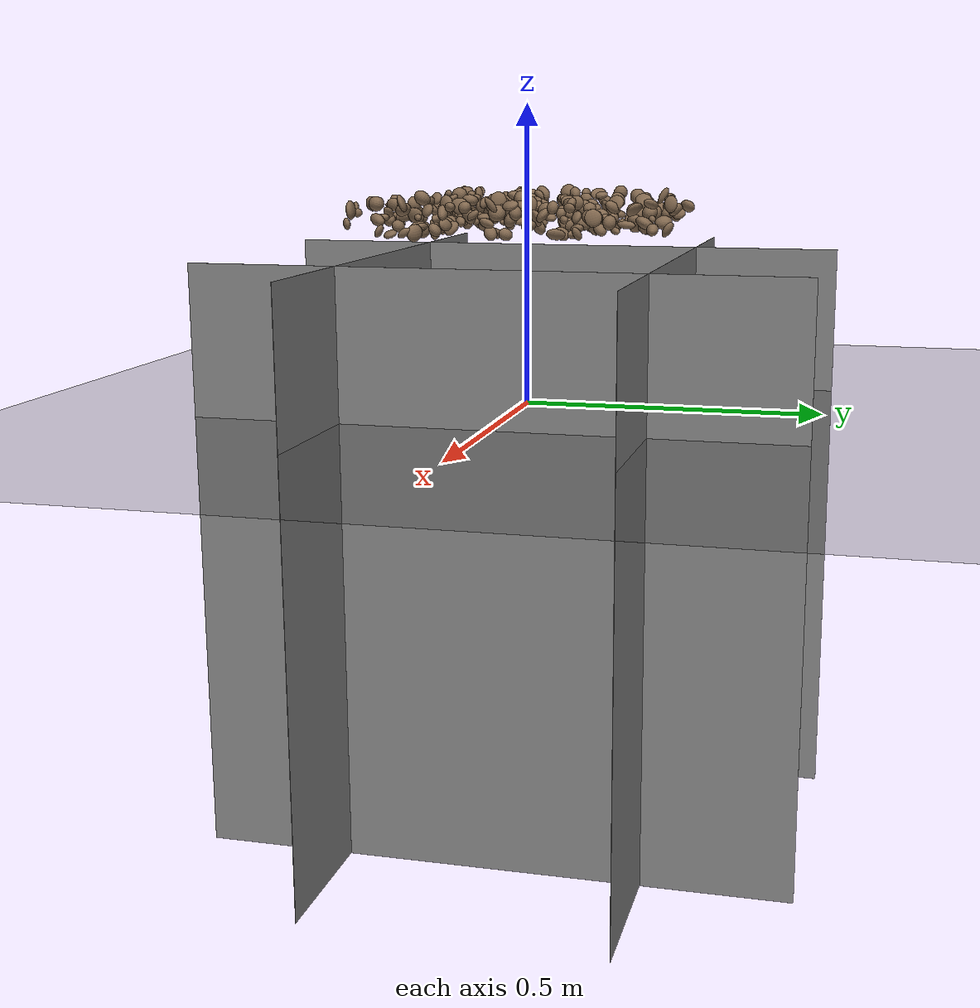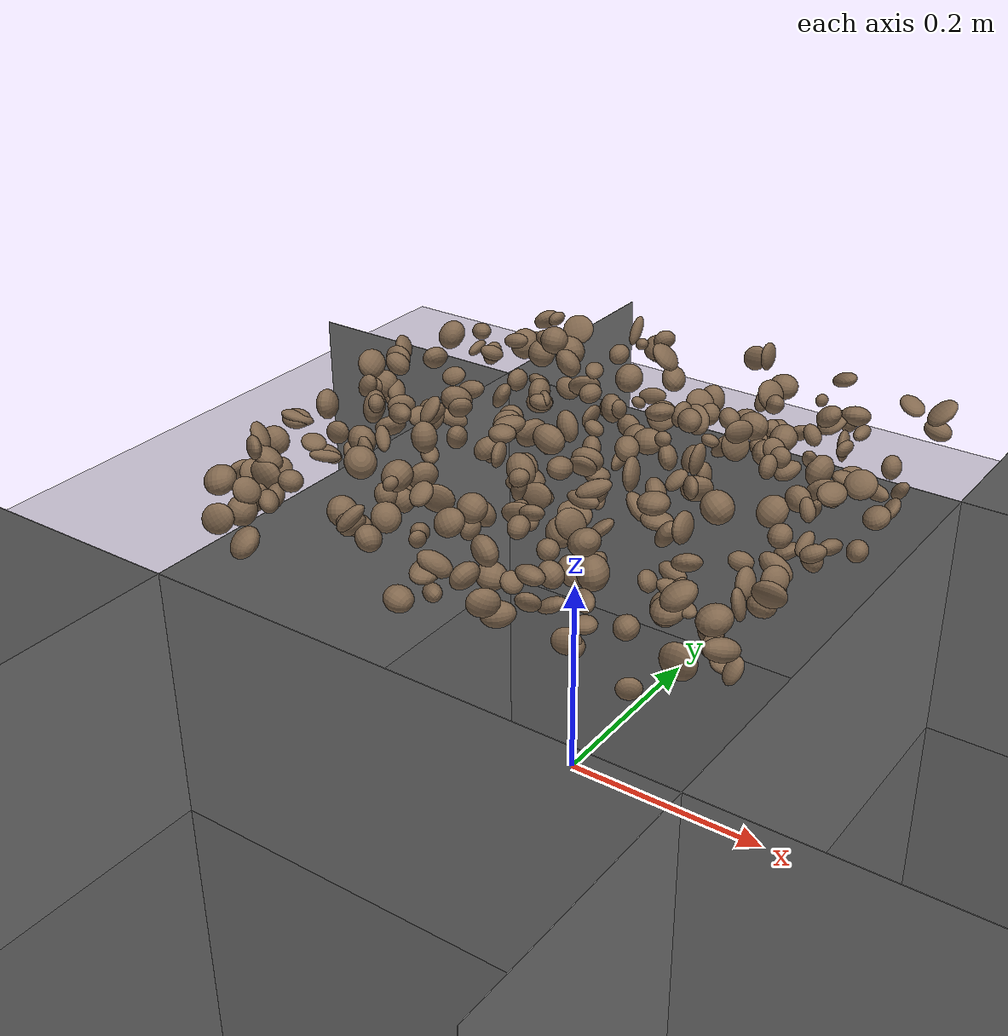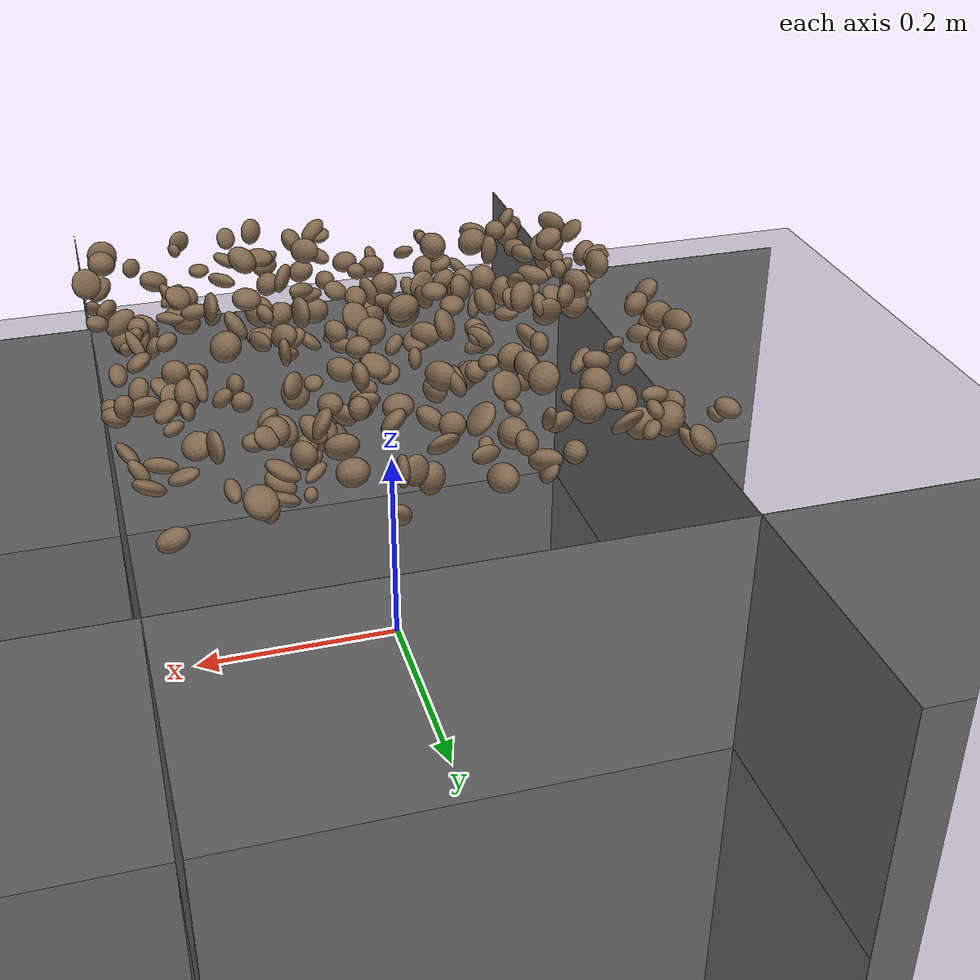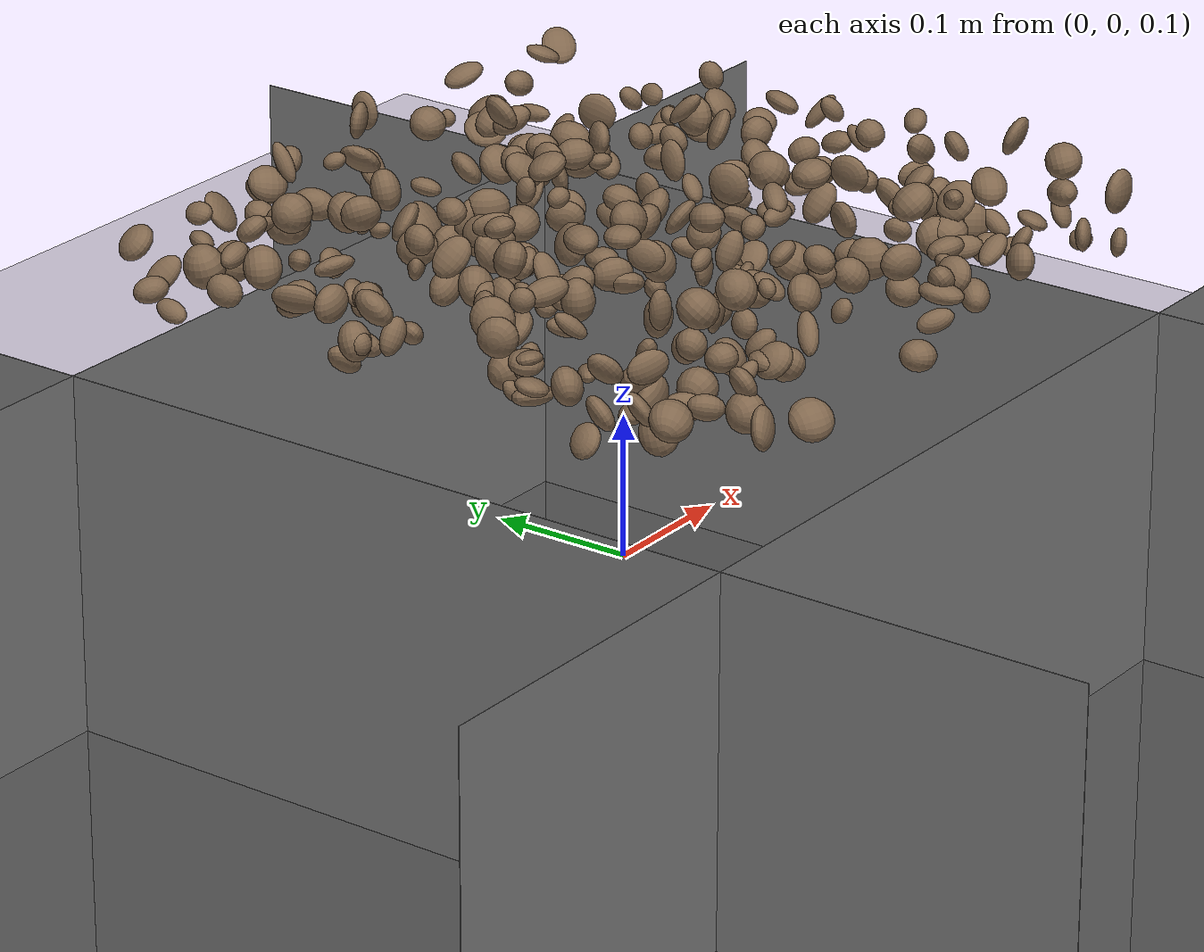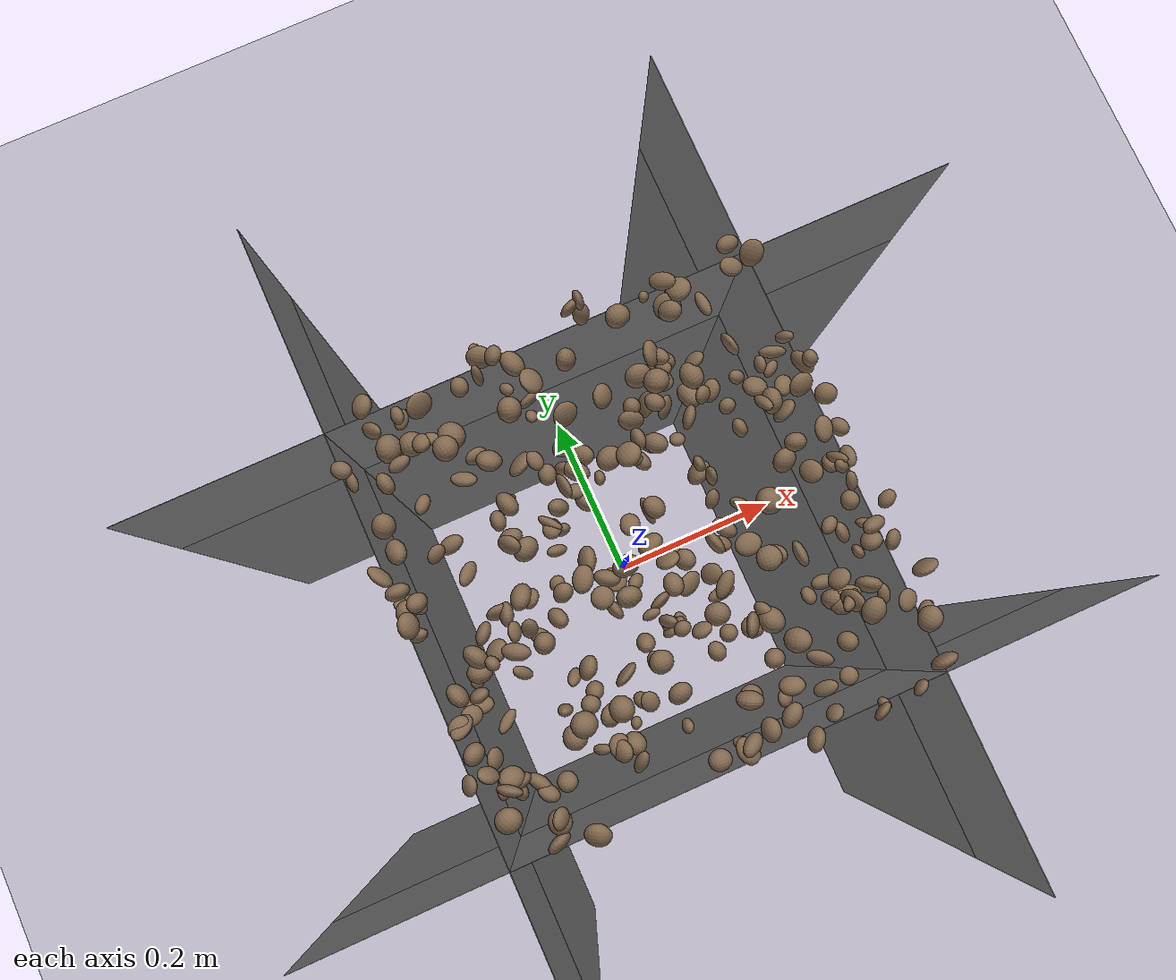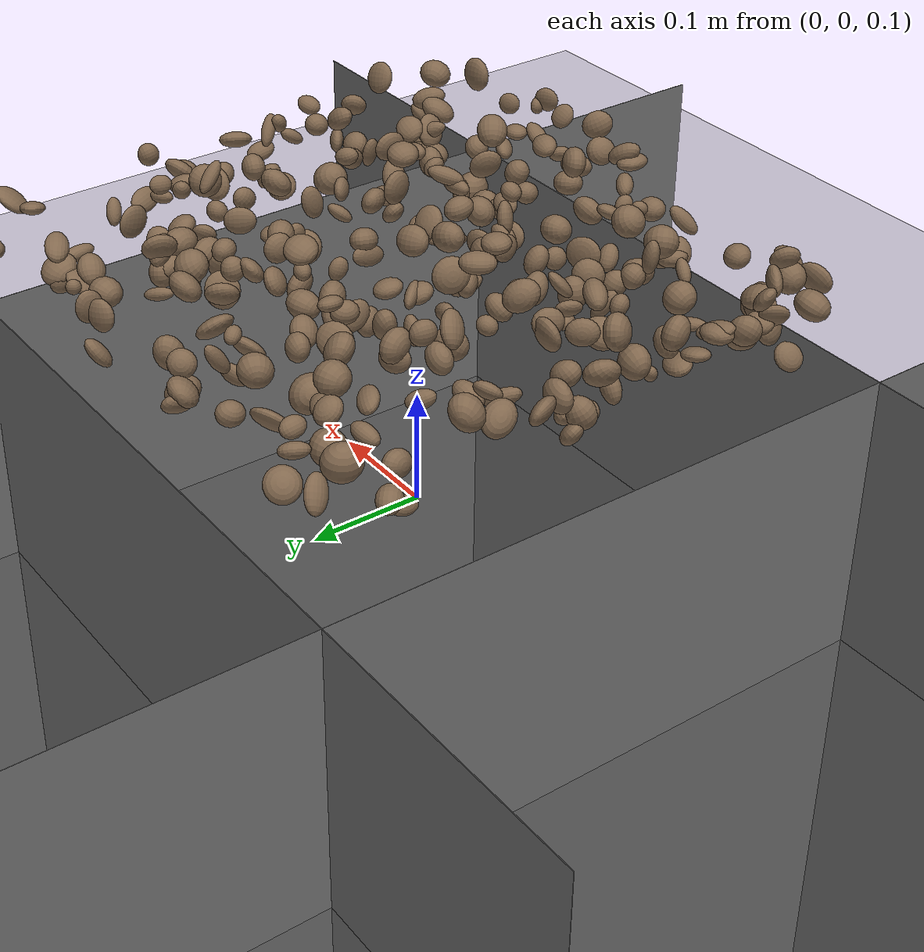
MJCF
<mujoco model="rocky_terrain_scene">

  <default>
    <default class="wall">
      <geom type="plane" size=".5 .5 .05" />
    </default>
  </default>

    <compiler angle="radian" inertiafromgeom="true" />
    <option timestep="0.002" gravity="0 0 -9.81" />

    <worldbody>

        <geom name="+x" class="wall" zaxis="1 0 0" pos="-.25 0 -.25" />
        <geom name="-x" class="wall" zaxis="-1 0 0" pos=".25 0 -.25" />
        <geom name="+y" class="wall" zaxis="0 1 0" pos="0 -.25 -.25" />
        <geom name="-y" class="wall" zaxis="0 -1 0" pos="0 .25 -.25" />

        <light name="sunlight" pos="5 5 5" dir="-1 -1 -1" diffuse="1 1 1" specular="0.5 0.5 0.5" ambient="0.5 0.5 0.5" />

        <geom name="ground_plane" type="plane" size="50 50 0.1" rgba="0.3 0.3 0.3 1" />

        <body name="rocky_terrain_body">

        </body>
    <body name="rock1" pos="0.2204277240630934 -0.003386675178600529 0.3031079007103576"><joint type="free" /><geom type="ellipsoid" size="0.009903243753443204 0.012116458608563705 0.008274277321616943" quat="0.20329071905814353 0.19478862764683588 0.19456422687004707 0.4073564264249736" rgba="0.5 0.4 0.3 1" /><inertial pos="0.2204277240630934 -0.003386675178600529 0.3031079007103576" quat="0.20329071905814353 0.19478862764683588 0.19456422687004707 0.4073564264249736" mass="3.47971664005333e-05" /></body><body name="rock2" pos="-0.11437150662998818 0.05055060620801938 0.33434872486975564"><joint type="free" /><geom type="ellipsoid" size="0.00686888280032613 0.010787719951870823 0.014916087594503705" quat="0.5934451915276721 0.15131710548294564 0.1789809396383918 0.07625676335099055" rgba="0.5 0.4 0.3 1" /><inertial pos="-0.11437150662998818 0.05055060620801938 0.33434872486975564" quat="0.5934451915276721 0.15131710548294564 0.1789809396383918 0.07625676335099055" mass="2.4329898344080013e-05" /></body><body name="rock3" pos="0.22070725455989337 0.07979785074141621 0.3322061245836547"><joint type="free" /><geom type="ellipsoid" size="0.013511065604176791 0.012964090706670643 0.006882809682661482" quat="0.5978136363985537 0.2696427116690561 0.009476209512961534 0.12306744241942855" rgba="0.5 0.4 0.3 1" /><inertial pos="0.22070725455989337 0.07979785074141621 0.3322061245836547" quat="0.5978136363985537 0.2696427116690561 0.009476209512961534 0.12306744241942855" mass="4.6478662539073054e-05" /></body><body name="rock4" pos="0.15706090324708938 -0.10952730632208024 0.32120905726663573"><joint type="free" /><geom type="ellipsoid" size="0.007339909702707535 0.007156382628598341 0.012376414020775543" quat="0.2562267050528351 0.26926324582508926 0.28208013771328283 0.1924299114087928" rgba="0.5 0.4 0.3 1" /><inertial pos="0.15706090324708938 -0.10952730632208024 0.32120905726663573" quat="0.2562267050528351 0.26926324582508926 0.28208013771328283 0.1924299114087928" mass="1.4050102411674335e-05" /></body><body name="rock5" pos="-0.05905793375064772 0.1790984132904629 0.31819112287635953"><joint type="free" /><geom type="ellipsoid" size="0.01378323257009327 0.013030073230074293 0.012445470733112536" quat="0.21924676409281602 0.35256676281145416 0.05532314205181648 0.37286333104391334" rgba="0.5 0.4 0.3 1" /><inertial pos="-0.05905793375064772 0.1790984132904629 0.31819112287635953" quat="0.21924676409281602 0.35256676281145416 0.05532314205181648 0.37286333104391334" mass="2.533525882984351e-05" /></body><body name="rock6" pos="0.1770821422104758 -0.1292414970686171 0.30855747343149975"><joint type="free" /><geom type="ellipsoid" size="0.007790703826285475 0.0054609494822497285 0.014701328174844146" quat="0.2763540793758833 0.3151543988028929 0.17397817750080832 0.2345133443204154" rgba="0.5 0.4 0.3 1" /><inertial pos="0.1770821422104758 -0.1292414970686171 0.30855747343149975" quat="0.2763540793758833 0.3151543988028929 0.17397817750080832 0.2345133443204154" mass="1.9248436523546096e-05" /></body><body name="rock7" pos="0.10524742042408375 -0.04503284415704134 0.31981409043068937"><joint type="free" /><geom type="ellipsoid" size="0.011923187133973853 0.006767942742588389 0.013821327112066874" quat="0.25127134639095056 0.24731835726951554 0.25300091297787763 0.2484093833616562" rgba="0.5 0.4 0.3 1" /><inertial pos="0.10524742042408375 -0.04503284415704134 0.31981409043068937" quat="0.25127134639095056 0.24731835726951554 0.25300091297787763 0.2484093833616562" mass="4.8154719422295154e-05" /></body><body name="rock8" pos="-0.005451890993032171 0.07439920099030578 0.3408492989568659"><joint type="free" /><geom type="ellipsoid" size="0.0053539786402851544 0.009459111714153826 0.007265108270787025" quat="0.06103465757067338 0.05528277776857544 0.35051141980071854 0.5331711448600327" rgba="0.5 0.4 0.3 1" /><inertial pos="-0.005451890993032171 0.07439920099030578 0.3408492989568659" quat="0.06103465757067338 0.05528277776857544 0.35051141980071854 0.5331711448600327" mass="6.832825794406137e-05" /></body><body name="rock9" pos="0.2173694538262197 -0.013187977231996828 0.3499115393281178"><joint type="free" /><geom type="ellipsoid" size="0.010004701583236748 0.006486863955696715 0.0061834615666806056" quat="0.08839273087714836 0.31088993203830767 0.10233337790176832 0.49838395918277556" rgba="0.5 0.4 0.3 1" /><inertial pos="0.2173694538262197 -0.013187977231996828 0.3499115393281178" quat="0.08839273087714836 0.31088993203830767 0.10233337790176832 0.49838395918277556" mass="3.985289668045328e-05" /></body><body name="rock10" pos="-0.06893807822294662 0.052825490591259905 0.3415459494503621"><joint type="free" /><geom type="ellipsoid" size="0.0050671394026913195 0.007719138309008072 0.013454922078081057" quat="0.40200843356566524 0.32983892500732886 0.10437474056564167 0.1637779008613642" rgba="0.5 0.4 0.3 1" /><inertial pos="-0.06893807822294662 0.052825490591259905 0.3415459494503621" quat="0.40200843356566524 0.32983892500732886 0.10437474056564167 0.1637779008613642" mass="3.7885089869604015e-05" /></body><body name="rock11" pos="0.22962170254155467 -0.22762154598524892 0.3358466102307838"><joint type="free" /><geom type="ellipsoid" size="0.006870735733717933 0.014936102068607338 0.01407221974859034" quat="0.2208282105359963 0.25697565953266754 0.2655570888772949 0.2566390410540413" rgba="0.5 0.4 0.3 1" /><inertial pos="0.22962170254155467 -0.22762154598524892 0.3358466102307838" quat="0.2208282105359963 0.25697565953266754 0.2655570888772949 0.2566390410540413" mass="2.3587590599067274e-05" /></body><body name="rock12" pos="-0.038273463607414904 -0.018522272046227584 0.3147250963547614"><joint type="free" /><geom type="ellipsoid" size="0.008518184582935231 0.011434523145633861 0.013608890278859864" quat="0.3302229334827402 0.3270748733212228 0.15432928706260804 0.18837290613342905" rgba="0.5 0.4 0.3 1" /><inertial pos="-0.038273463607414904 -0.018522272046227584 0.3147250963547614" quat="0.3302229334827402 0.3270748733212228 0.15432928706260804 0.18837290613342905" mass="5.934649830780949e-05" /></body><body name="rock13" pos="-0.06172138992804088 -0.01113453060192554 0.3439460805014466"><joint type="free" /><geom type="ellipsoid" size="0.01064906344540722 0.008117467823666766 0.014411437095781188" quat="0.1471960945600015 0.07964712703981967 0.38596909683887637 0.38718768156130245" rgba="0.5 0.4 0.3 1" /><inertial pos="-0.06172138992804088 -0.01113453060192554 0.3439460805014466" quat="0.1471960945600015 0.07964712703981967 0.38596909683887637 0.38718768156130245" mass="9.05656170683204e-05" /></body><body name="rock14" pos="-0.026302428942835743 -0.044758168618109495 0.3256292967666017"><joint type="free" /><geom type="ellipsoid" size="0.010656899890697933 0.014846811637637514 0.012405128627646804" quat="0.34038307745700336 0.12572625226969733 0.22275587450145284 0.31113479577184644" rgba="0.5 0.4 0.3 1" /><inertial pos="-0.026302428942835743 -0.044758168618109495 0.3256292967666017" quat="0.34038307745700336 0.12572625226969733 0.22275587450145284 0.31113479577184644" mass="9.017194879956782e-05" /></body><body name="rock15" pos="0.18832755309841454 -0.06080996607600081 0.3179800563018015"><joint type="free" /><geom type="ellipsoid" size="0.007401427641688747 0.010424453174911277 0.007725507444052107" quat="0.3010133453275846 0.015827496618508158 0.10905751171809328 0.5741016463358141" rgba="0.5 0.4 0.3 1" /><inertial pos="0.18832755309841454 -0.06080996607600081 0.3179800563018015" quat="0.3010133453275846 0.015827496618508158 0.10905751171809328 0.5741016463358141" mass="1.1613390787154893e-05" /></body><body name="rock16" pos="-0.05938280618347758 0.0456374443177483 0.30459173034153064"><joint type="free" /><geom type="ellipsoid" size="0.00620135389267022 0.012419998253817904 0.007368365325827461" quat="0.235134285436326 0.3226069072469899 0.27223801870586317 0.170020788610821" rgba="0.5 0.4 0.3 1" /><inertial pos="-0.05938280618347758 0.0456374443177483 0.30459173034153064" quat="0.235134285436326 0.3226069072469899 0.27223801870586317 0.170020788610821" mass="2.5046008680983792e-05" /></body><body name="rock17" pos="0.046160139187403415 -0.21883832334276776 0.33469870492594866"><joint type="free" /><geom type="ellipsoid" size="0.01263628034141132 0.011814842728627413 0.008548145603290456" quat="0.16554503314333083 0.4004351439595939 0.22224832285839902 0.21177150003867634" rgba="0.5 0.4 0.3 1" /><inertial pos="0.046160139187403415 -0.21883832334276776 0.33469870492594866" quat="0.16554503314333083 0.4004351439595939 0.22224832285839902 0.21177150003867634" mass="8.196921808532707e-05" /></body><body name="rock18" pos="0.05972033084749728 0.08309866667556898 0.3441845713109062"><joint type="free" /><geom type="ellipsoid" size="0.009882034992119273 0.01038501025370149 0.012442520176746592" quat="0.42798384563436576 0.2836779977353363 0.26843929147798984 0.01989886515230812" rgba="0.5 0.4 0.3 1" /><inertial pos="0.05972033084749728 0.08309866667556898 0.3441845713109062" quat="0.42798384563436576 0.2836779977353363 0.26843929147798984 0.01989886515230812" mass="1.3781394099508958e-05" /></body><body name="rock19" pos="-0.23999051798561116 0.19075574133955242 0.31946179910170003"><joint type="free" /><geom type="ellipsoid" size="0.011506142021836079 0.00836956528157521 0.009156627285735304" quat="0.18613158067815744 0.09481579388520493 0.3764704377442614 0.3425821876923762" rgba="0.5 0.4 0.3 1" /><inertial pos="-0.23999051798561116 0.19075574133955242 0.31946179910170003" quat="0.18613158067815744 0.09481579388520493 0.3764704377442614 0.3425821876923762" mass="4.470203544813508e-05" /></body><body name="rock20" pos="-0.03376377871562414 0.10023211846463115 0.32594784199746496"><joint type="free" /><geom type="ellipsoid" size="0.006774878298895217 0.013074258033521899 0.0064383998944559885" quat="0.02714599191640444 0.2508240674966374 0.34924325158642155 0.3727866890005366" rgba="0.5 0.4 0.3 1" /><inertial pos="-0.03376377871562414 0.10023211846463115 0.32594784199746496" quat="0.02714599191640444 0.2508240674966374 0.34924325158642155 0.3727866890005366" mass="6.080742912387371e-05" /></body><body name="rock21" pos="-0.08467426219673241 -0.013983858655511827 0.3161883332169424"><joint type="free" /><geom type="ellipsoid" size="0.009682899074306348 0.009076871710563053 0.01196009711506611" quat="0.1851583981211351 0.13692915019382065 0.17517780562854235 0.502734646056502" rgba="0.5 0.4 0.3 1" /><inertial pos="-0.08467426219673241 -0.013983858655511827 0.3161883332169424" quat="0.1851583981211351 0.13692915019382065 0.17517780562854235 0.502734646056502" mass="2.5107535365185975e-05" /></body><body name="rock22" pos="-0.17520534989341413 -0.050285877248557875 0.348774977847652"><joint type="free" /><geom type="ellipsoid" size="0.008422370230086879 0.008030803090260963 0.006717776310653343" quat="0.38275413449655066 0.033613536370679785 0.3764525824128283 0.20717974671994135" rgba="0.5 0.4 0.3 1" /><inertial pos="-0.17520534989341413 -0.050285877248557875 0.348774977847652" quat="0.38275413449655066 0.033613536370679785 0.3764525824128283 0.20717974671994135" mass="5.617157965230326e-05" /></body><body name="rock23" pos="-0.23348778910190765 0.05144802663556752 0.34126293006598296"><joint type="free" /><geom type="ellipsoid" size="0.008333826810566044 0.013166886749926405 0.011793172688519614" quat="0.07489328926518146 0.42916245823437066 0.4194143095216868 0.07652994297876116" rgba="0.5 0.4 0.3 1" /><inertial pos="-0.23348778910190765 0.05144802663556752 0.34126293006598296" quat="0.07489328926518146 0.42916245823437066 0.4194143095216868 0.07652994297876116" mass="6.758813361218385e-05" /></body><body name="rock24" pos="0.13435942055503997 0.23174954456633262 0.3464853627192621"><joint type="free" /><geom type="ellipsoid" size="0.014323440105840735 0.006228930863246178 0.009184932198522452" quat="0.1882155434303393 0.01103225663826409 0.3721400284081536 0.42861217152324294" rgba="0.5 0.4 0.3 1" /><inertial pos="0.13435942055503997 0.23174954456633262 0.3464853627192621" quat="0.1882155434303393 0.01103225663826409 0.3721400284081536 0.42861217152324294" mass="5.0007939211642565e-05" /></body><body name="rock25" pos="0.2044886828014718 0.08662275220370869 0.32909264319183285"><joint type="free" /><geom type="ellipsoid" size="0.012438476969004797 0.006565710151432086 0.009309258464870428" quat="0.35349090601683675 0.33666885339732333 0.2292140306247674 0.0806262099610725" rgba="0.5 0.4 0.3 1" /><inertial pos="0.2044886828014718 0.08662275220370869 0.32909264319183285" quat="0.35349090601683675 0.33666885339732333 0.2292140306247674 0.0806262099610725" mass="7.695130632761802e-05" /></body><body name="rock26" pos="-0.025559808132672113 0.06225784346186092 0.30165578703237955"><joint type="free" /><geom type="ellipsoid" size="0.00846512072792418 0.011844368539608467 0.011920972829635265" quat="0.37703055099779353 0.40099605841235725 0.13232308064577475 0.08965030994407451" rgba="0.5 0.4 0.3 1" /><inertial pos="-0.025559808132672113 0.06225784346186092 0.30165578703237955" quat="0.37703055099779353 0.40099605841235725 0.13232308064577475 0.08965030994407451" mass="6.471715479682348e-05" /></body><body name="rock27" pos="0.24512003902421392 -0.17594161283415916 0.30516601330844095"><joint type="free" /><geom type="ellipsoid" size="0.01113057678686483 0.00514496246067801 0.0071137036388666895" quat="0.15317773854876862 0.423931496667662 0.06134608655872058 0.3615446782248488" rgba="0.5 0.4 0.3 1" /><inertial pos="0.24512003902421392 -0.17594161283415916 0.30516601330844095" quat="0.15317773854876862 0.423931496667662 0.06134608655872058 0.3615446782248488" mass="9.782445671277332e-05" /></body><body name="rock28" pos="-0.1860028615834799 -0.10742178002448272 0.31865778021509794"><joint type="free" /><geom type="ellipsoid" size="0.013631000867670447 0.005086723638103846 0.006002547697520567" quat="0.3990751626874207 0.3404263591266815 0.15101720318753162 0.10948127499836607" rgba="0.5 0.4 0.3 1" /><inertial pos="-0.1860028615834799 -0.10742178002448272 0.31865778021509794" quat="0.3990751626874207 0.3404263591266815 0.15101720318753162 0.10948127499836607" mass="8.91290193082607e-05" /></body><body name="rock29" pos="0.023152957015922015 -0.027423187636523405 0.3364006080200833"><joint type="free" /><geom type="ellipsoid" size="0.012148396239312579 0.013526344340269735 0.005690697148353125" quat="0.3051342040243684 0.5664077883096423 0.12333111383230196 0.005126893833687313" rgba="0.5 0.4 0.3 1" /><inertial pos="0.023152957015922015 -0.027423187636523405 0.3364006080200833" quat="0.3051342040243684 0.5664077883096423 0.12333111383230196 0.005126893833687313" mass="2.720981016312634e-05" /></body><body name="rock30" pos="0.11346540811881328 -0.20533883971330408 0.3267595606458643"><joint type="free" /><geom type="ellipsoid" size="0.007725586766836545 0.005765182717498493 0.013223369859463298" quat="0.3228883451018158 0.18107926139228706 0.18030031814960878 0.31573207535628833" rgba="0.5 0.4 0.3 1" /><inertial pos="0.11346540811881328 -0.20533883971330408 0.3267595606458643" quat="0.3228883451018158 0.18107926139228706 0.18030031814960878 0.31573207535628833" mass="9.27792710942715e-05" /></body><body name="rock31" pos="-0.10935192040817993 0.1510285537485615 0.30547548600079505"><joint type="free" /><geom type="ellipsoid" size="0.010111925280309776 0.0066553399617201225 0.012196702268024882" quat="0.051639964084381554 0.4828761704034938 0.13155319907040292 0.3339306664417217" rgba="0.5 0.4 0.3 1" /><inertial pos="-0.10935192040817993 0.1510285537485615 0.30547548600079505" quat="0.051639964084381554 0.4828761704034938 0.13155319907040292 0.3339306664417217" mass="8.362531277538388e-05" /></body><body name="rock32" pos="-0.11766867172685291 -0.13986919305441559 0.3460518128556446"><joint type="free" /><geom type="ellipsoid" size="0.013294629107496896 0.013918889156877511 0.012543820059977728" quat="0.44160650306833255 0.20807807542317092 0.04654079525026338 0.3037746262582331" rgba="0.5 0.4 0.3 1" /><inertial pos="-0.11766867172685291 -0.13986919305441559 0.3460518128556446" quat="0.44160650306833255 0.20807807542317092 0.04654079525026338 0.3037746262582331" mass="1.3617567265321842e-05" /></body><body name="rock33" pos="0.21577766837556017 0.12701511979869906 0.30332641197235805"><joint type="free" /><geom type="ellipsoid" size="0.006088337956164576 0.006959695028949445 0.014219303152874545" quat="0.35382090166265523 0.24403101617136483 0.26941231371938756 0.1327357684465923" rgba="0.5 0.4 0.3 1" /><inertial pos="0.21577766837556017 0.12701511979869906 0.30332641197235805" quat="0.35382090166265523 0.24403101617136483 0.26941231371938756 0.1327357684465923" mass="9.074165704492147e-05" /></body><body name="rock34" pos="0.036733937161948116 0.07948529038482421 0.321677967892284"><joint type="free" /><geom type="ellipsoid" size="0.006679098755080751 0.006874944312317294 0.00785107411609466" quat="0.28074623779085495 0.26918806833255005 0.12222855353349116 0.3278371403431039" rgba="0.5 0.4 0.3 1" /><inertial pos="0.036733937161948116 0.07948529038482421 0.321677967892284" quat="0.28074623779085495 0.26918806833255005 0.12222855353349116 0.3278371403431039" mass="7.399232362942226e-05" /></body><body name="rock35" pos="-0.1499408321115041 -0.049368198320329015 0.34596303964013503"><joint type="free" /><geom type="ellipsoid" size="0.009046161270341451 0.00836453378692004 0.01496028481905529" quat="0.2963135152318164 0.3218433005098886 0.0909513830680865 0.2908918011902086" rgba="0.5 0.4 0.3 1" /><inertial pos="-0.1499408321115041 -0.049368198320329015 0.34596303964013503" quat="0.2963135152318164 0.3218433005098886 0.0909513830680865 0.2908918011902086" mass="4.0065303332902426e-05" /></body><body name="rock36" pos="0.0602150808797155 0.08966755845234503 0.30513761251297317"><joint type="free" /><geom type="ellipsoid" size="0.012470879734422473 0.011984747579264956 0.007281418225595271" quat="0.04046049391890487 0.28735571113547104 0.3803114664688021 0.291872328476822" rgba="0.5 0.4 0.3 1" /><inertial pos="0.0602150808797155 0.08966755845234503 0.30513761251297317" quat="0.04046049391890487 0.28735571113547104 0.3803114664688021 0.291872328476822" mass="2.6621268150661033e-05" /></body><body name="rock37" pos="0.019383318641319758 -0.22328069606833828 0.31325117428082944"><joint type="free" /><geom type="ellipsoid" size="0.012486289210638393 0.0071882647876430105 0.007099213914036064" quat="0.14627054681458151 0.15964621575955845 0.5350072498570991 0.15907598756876096" rgba="0.5 0.4 0.3 1" /><inertial pos="0.019383318641319758 -0.22328069606833828 0.31325117428082944" quat="0.14627054681458151 0.15964621575955845 0.5350072498570991 0.15907598756876096" mass="8.336037089554946e-05" /></body><body name="rock38" pos="0.0506064511850185 0.2453932552519827 0.3012755250748866"><joint type="free" /><geom type="ellipsoid" size="0.008825971717670182 0.014149405840307563 0.006326998648092056" quat="0.053861782297539615 0.09215337414625592 0.5592569085477952 0.2947279350084092" rgba="0.5 0.4 0.3 1" /><inertial pos="0.0506064511850185 0.2453932552519827 0.3012755250748866" quat="0.053861782297539615 0.09215337414625592 0.5592569085477952 0.2947279350084092" mass="3.0333099408394272e-05" /></body><body name="rock39" pos="0.05721278016207837 -0.07874193561138998 0.3386586143664949"><joint type="free" /><geom type="ellipsoid" size="0.006936240920967202 0.00658919905641132 0.013991230701284718" quat="0.08680555490092029 0.40338761561754416 0.11675651817135015 0.39305031131018553" rgba="0.5 0.4 0.3 1" /><inertial pos="0.05721278016207837 -0.07874193561138998 0.3386586143664949" quat="0.08680555490092029 0.40338761561754416 0.11675651817135015 0.39305031131018553" mass="8.319776208949235e-05" /></body><body name="rock40" pos="-0.1768528032390594 -0.1878466496478135 0.313273366012355"><joint type="free" /><geom type="ellipsoid" size="0.007845435163769529 0.009123098158439674 0.011877597447915365" quat="0.2939664495564098 0.4489152188135679 0.01486501485742465 0.24225331677259762" rgba="0.5 0.4 0.3 1" /><inertial pos="-0.1768528032390594 -0.1878466496478135 0.313273366012355" quat="0.2939664495564098 0.4489152188135679 0.01486501485742465 0.24225331677259762" mass="3.493700191990061e-05" /></body><body name="rock41" pos="0.22320458743452254 -0.09230636598169023 0.30695488409895477"><joint type="free" /><geom type="ellipsoid" size="0.011410238682029753 0.011367064980063117 0.008733849820893884" quat="0.3000049712820174 0.6375810510812199 0.03957270765571002 0.022841269981052667" rgba="0.5 0.4 0.3 1" /><inertial pos="0.22320458743452254 -0.09230636598169023 0.30695488409895477" quat="0.3000049712820174 0.6375810510812199 0.03957270765571002 0.022841269981052667" mass="5.21299471261236e-05" /></body><body name="rock42" pos="0.030714767472068194 -0.128995906184377 0.32861681667686604"><joint type="free" /><geom type="ellipsoid" size="0.010540864914804899 0.008926228415390286 0.00873003118628697" quat="0.15684076652038673 0.2830838256253678 0.2594317653631446 0.30064364249110087" rgba="0.5 0.4 0.3 1" /><inertial pos="0.030714767472068194 -0.128995906184377 0.32861681667686604" quat="0.15684076652038673 0.2830838256253678 0.2594317653631446 0.30064364249110087" mass="5.5447030650543545e-05" /></body><body name="rock43" pos="0.20331468712910616 -0.13186410360020834 0.3001271740517728"><joint type="free" /><geom type="ellipsoid" size="0.008156621153452805 0.014011461159483759 0.014463406168455165" quat="0.3078824144494726 0.337231660307058 0.20847179422502748 0.14641413101844195" rgba="0.5 0.4 0.3 1" /><inertial pos="0.20331468712910616 -0.13186410360020834 0.3001271740517728" quat="0.3078824144494726 0.337231660307058 0.20847179422502748 0.14641413101844195" mass="2.5026330098494296e-05" /></body><body name="rock44" pos="-0.013528006560558858 -0.06960987428276078 0.328694113122843"><joint type="free" /><geom type="ellipsoid" size="0.00990208776605906 0.005398637420483038 0.006483379534004766" quat="0.0011691284820844617 0.8275937097081032 0.03343598953238001 0.13780117227743233" rgba="0.5 0.4 0.3 1" /><inertial pos="-0.013528006560558858 -0.06960987428276078 0.328694113122843" quat="0.0011691284820844617 0.8275937097081032 0.03343598953238001 0.13780117227743233" mass="2.383009017557947e-05" /></body><body name="rock45" pos="0.1434769481911255 0.09037230489964698 0.3302710060830735"><joint type="free" /><geom type="ellipsoid" size="0.00782419973334151 0.009027610666836152 0.008765991982274852" quat="0.2439505312426046 0.2029798262551783 0.3455795704060963 0.20749007209612075" rgba="0.5 0.4 0.3 1" /><inertial pos="0.1434769481911255 0.09037230489964698 0.3302710060830735" quat="0.2439505312426046 0.2029798262551783 0.3455795704060963 0.20749007209612075" mass="1.1398201727374681e-05" /></body><body name="rock46" pos="0.20490482584332181 0.21750942925043465 0.3449565619578856"><joint type="free" /><geom type="ellipsoid" size="0.009957444887163124 0.012673004599528937 0.005211295961306708" quat="0.5097168125880063 0.1127262713989179 0.04521387006581407 0.3323430459472618" rgba="0.5 0.4 0.3 1" /><inertial pos="0.20490482584332181 0.21750942925043465 0.3449565619578856" quat="0.5097168125880063 0.1127262713989179 0.04521387006581407 0.3323430459472618" mass="8.766298157928828e-05" /></body><body name="rock47" pos="0.18561557311827348 0.07641907339262743 0.3357487103920604"><joint type="free" /><geom type="ellipsoid" size="0.013347083189991713 0.013827399897213013 0.010187635538331075" quat="0.3028749003897183 0.24339510064651387 0.31117781660552357 0.14255218235824418" rgba="0.5 0.4 0.3 1" /><inertial pos="0.18561557311827348 0.07641907339262743 0.3357487103920604" quat="0.3028749003897183 0.24339510064651387 0.31117781660552357 0.14255218235824418" mass="8.694255342997651e-05" /></body><body name="rock48" pos="0.20674093041254854 -0.0968642907050809 0.30452363002817323"><joint type="free" /><geom type="ellipsoid" size="0.008088796832508762 0.013953029879031492 0.005153515476217783" quat="0.2489937979451368 0.19123056720559117 0.2514253664362742 0.3083502684129978" rgba="0.5 0.4 0.3 1" /><inertial pos="0.20674093041254854 -0.0968642907050809 0.30452363002817323" quat="0.2489937979451368 0.19123056720559117 0.2514253664362742 0.3083502684129978" mass="9.211391435020742e-05" /></body><body name="rock49" pos="-0.08608577468032269 -0.002200087758092162 0.30533016538556895"><joint type="free" /><geom type="ellipsoid" size="0.00866491652819053 0.0076953624637444715 0.0074448645263670175" quat="0.29182705035902506 0.4601088670756177 0.049287640836720006 0.1987764417286372" rgba="0.5 0.4 0.3 1" /><inertial pos="-0.08608577468032269 -0.002200087758092162 0.30533016538556895" quat="0.29182705035902506 0.4601088670756177 0.049287640836720006 0.1987764417286372" mass="6.063060751613899e-05" /></body><body name="rock50" pos="0.15940977364288356 -0.2421142452021905 0.3279983399944395"><joint type="free" /><geom type="ellipsoid" size="0.007135057697297819 0.007691323545094166 0.00529050065945129" quat="0.04753819889738434 0.3944473466271855 0.1822067137826379 0.37580774069279227" rgba="0.5 0.4 0.3 1" /><inertial pos="0.15940977364288356 -0.2421142452021905 0.3279983399944395" quat="0.04753819889738434 0.3944473466271855 0.1822067137826379 0.37580774069279227" mass="2.3437445261499562e-05" /></body><body name="rock51" pos="-0.12292368198163311 -0.0442682514351066 0.31266138846584846"><joint type="free" /><geom type="ellipsoid" size="0.008046723762943514 0.006311814848709237 0.012184309991098097" quat="0.32110396024782945 0.3776202804020249 0.19626262827089688 0.10501313107924883" rgba="0.5 0.4 0.3 1" /><inertial pos="-0.12292368198163311 -0.0442682514351066 0.31266138846584846" quat="0.32110396024782945 0.3776202804020249 0.19626262827089688 0.10501313107924883" mass="9.560336476214009e-05" /></body><body name="rock52" pos="-0.0731340203853253 0.026842440973451898 0.320590329817188"><joint type="free" /><geom type="ellipsoid" size="0.005794949703379914 0.007148555146877877 0.011046152733489228" quat="0.20955119009799167 0.31743668692136434 0.3049901561559774 0.16802196682466652" rgba="0.5 0.4 0.3 1" /><inertial pos="-0.0731340203853253 0.026842440973451898 0.320590329817188" quat="0.20955119009799167 0.31743668692136434 0.3049901561559774 0.16802196682466652" mass="5.173791264512681e-05" /></body><body name="rock53" pos="-0.20580181996062552 -0.08126637442400814 0.30429166235280564"><joint type="free" /><geom type="ellipsoid" size="0.014499771343645204 0.010374130173584788 0.006464876198486249" quat="0.11838315050469733 0.054526646270551364 0.11511946993195338 0.7119707332927979" rgba="0.5 0.4 0.3 1" /><inertial pos="-0.20580181996062552 -0.08126637442400814 0.30429166235280564" quat="0.11838315050469733 0.054526646270551364 0.11511946993195338 0.7119707332927979" mass="7.321939419172003e-05" /></body><body name="rock54" pos="0.1401165409703411 -0.11660971820449134 0.31168869877492195"><joint type="free" /><geom type="ellipsoid" size="0.009587491054048877 0.009113494107482105 0.006686328863692257" quat="0.3562629691181313 0.12100908023923437 0.2311039054783518 0.29162404516428253" rgba="0.5 0.4 0.3 1" /><inertial pos="0.1401165409703411 -0.11660971820449134 0.31168869877492195" quat="0.3562629691181313 0.12100908023923437 0.2311039054783518 0.29162404516428253" mass="8.962451400098959e-05" /></body><body name="rock55" pos="0.19926771162744528 -0.07259257388774848 0.3083210087706823"><joint type="free" /><geom type="ellipsoid" size="0.009686839952574995 0.013100608450362754 0.006363459159849135" quat="0.40865219119844304 0.1489957974746707 0.26431059942052443 0.17804141190636183" rgba="0.5 0.4 0.3 1" /><inertial pos="0.19926771162744528 -0.07259257388774848 0.3083210087706823" quat="0.40865219119844304 0.1489957974746707 0.26431059942052443 0.17804141190636183" mass="7.100645089979193e-05" /></body><body name="rock56" pos="-0.1952510678940077 0.24141176504537287 0.32545726097134875"><joint type="free" /><geom type="ellipsoid" size="0.012955517481185942 0.013143820066522274 0.007869806805153434" quat="0.18439866045678588 0.41848187715362184 0.29524078267537507 0.10187867971421723" rgba="0.5 0.4 0.3 1" /><inertial pos="-0.1952510678940077 0.24141176504537287 0.32545726097134875" quat="0.18439866045678588 0.41848187715362184 0.29524078267537507 0.10187867971421723" mass="1.262642330472655e-05" /></body><body name="rock57" pos="0.0723661502697227 -0.11913088675009365 0.34015232602799134"><joint type="free" /><geom type="ellipsoid" size="0.014048606140853175 0.01196945999726458 0.006178907961028418" quat="0.4484075131725779 0.200203618771921 0.28943962851800265 0.06194923953749861" rgba="0.5 0.4 0.3 1" /><inertial pos="0.0723661502697227 -0.11913088675009365 0.34015232602799134" quat="0.4484075131725779 0.200203618771921 0.28943962851800265 0.06194923953749861" mass="6.892679822723092e-05" /></body><body name="rock58" pos="-0.03532153760735823 0.18326950365830064 0.30445718843654523"><joint type="free" /><geom type="ellipsoid" size="0.005080436241870354 0.00811610977466687 0.013113077413461984" quat="0.2334269383881203 0.18946335380044557 0.27450233440011923 0.30260737341131483" rgba="0.5 0.4 0.3 1" /><inertial pos="-0.03532153760735823 0.18326950365830064 0.30445718843654523" quat="0.2334269383881203 0.18946335380044557 0.27450233440011923 0.30260737341131483" mass="2.9078532748915595e-05" /></body><body name="rock59" pos="-0.2293003144524159 -0.09374753560770344 0.33672120771507597"><joint type="free" /><geom type="ellipsoid" size="0.012732971721093337 0.007585483173107414 0.010896507940528693" quat="0.39146514172155866 0.4552887899050153 0.09106089962257202 0.06218516875085391" rgba="0.5 0.4 0.3 1" /><inertial pos="-0.2293003144524159 -0.09374753560770344 0.33672120771507597" quat="0.39146514172155866 0.4552887899050153 0.09106089962257202 0.06218516875085391" mass="1.0977430339846025e-05" /></body><body name="rock60" pos="0.13968673764442452 0.11541521363095464 0.30576117125939484"><joint type="free" /><geom type="ellipsoid" size="0.0089789018115474 0.00752809592050125 0.012489256367060492" quat="0.1754097045151956 0.08536014881192167 0.30972190155851487 0.4295082451143679" rgba="0.5 0.4 0.3 1" /><inertial pos="0.13968673764442452 0.11541521363095464 0.30576117125939484" quat="0.1754097045151956 0.08536014881192167 0.30972190155851487 0.4295082451143679" mass="3.733518938559421e-05" /></body><body name="rock61" pos="-0.12880748590245678 -0.11988564851648753 0.34421335007983556"><joint type="free" /><geom type="ellipsoid" size="0.006028756484525887 0.014090235053582818 0.007489937566639469" quat="0.294300266077385 0.2980678017990264 0.1797848088761512 0.2278471232474373" rgba="0.5 0.4 0.3 1" /><inertial pos="-0.12880748590245678 -0.11988564851648753 0.34421335007983556" quat="0.294300266077385 0.2980678017990264 0.1797848088761512 0.2278471232474373" mass="9.28469871693393e-05" /></body><body name="rock62" pos="0.07458499467280993 -0.21713385297927373 0.31104378184925463"><joint type="free" /><geom type="ellipsoid" size="0.009335980299068987 0.010097352806954604 0.013509269820860936" quat="0.22737401398383958 0.11300639610673277 0.3296839155809853 0.3299356743284424" rgba="0.5 0.4 0.3 1" /><inertial pos="0.07458499467280993 -0.21713385297927373 0.31104378184925463" quat="0.22737401398383958 0.11300639610673277 0.3296839155809853 0.3299356743284424" mass="4.6580829044110866e-05" /></body><body name="rock63" pos="0.1450442377415775 0.06452400945341935 0.3328369919629863"><joint type="free" /><geom type="ellipsoid" size="0.007070005856016788 0.009096993269399997 0.010649828487016337" quat="0.2636026262078455 0.6894748905394263 0.011575947167455332 0.035346536085272884" rgba="0.5 0.4 0.3 1" /><inertial pos="0.1450442377415775 0.06452400945341935 0.3328369919629863" quat="0.2636026262078455 0.6894748905394263 0.011575947167455332 0.035346536085272884" mass="7.613235208987318e-05" /></body><body name="rock64" pos="-0.17476830888105765 -0.21288686317411148 0.3345430360666532"><joint type="free" /><geom type="ellipsoid" size="0.010966818631676985 0.012194501083510584 0.006450129662218139" quat="0.306656310271682 0.2764317094656614 0.06233436207451094 0.3545776181881457" rgba="0.5 0.4 0.3 1" /><inertial pos="-0.17476830888105765 -0.21288686317411148 0.3345430360666532" quat="0.306656310271682 0.2764317094656614 0.06233436207451094 0.3545776181881457" mass="6.632374664768504e-05" /></body><body name="rock65" pos="0.04282759854093615 0.07850067612862405 0.3064067518706527"><joint type="free" /><geom type="ellipsoid" size="0.013225800063569385 0.011786384770839188 0.00801163729153886" quat="0.2805262625672484 0.1182503188049772 0.2949544478509689 0.3062689707768055" rgba="0.5 0.4 0.3 1" /><inertial pos="0.04282759854093615 0.07850067612862405 0.3064067518706527" quat="0.2805262625672484 0.1182503188049772 0.2949544478509689 0.3062689707768055" mass="2.4414337293142903e-05" /></body><body name="rock66" pos="-0.027969093354551777 -0.11283473576941233 0.30033342206879127"><joint type="free" /><geom type="ellipsoid" size="0.009792966772620149 0.009432868706487862 0.006888724954884765" quat="0.12961353767977102 0.4543056861836446 0.05230284580377287 0.3637779303328116" rgba="0.5 0.4 0.3 1" /><inertial pos="-0.027969093354551777 -0.11283473576941233 0.30033342206879127" quat="0.12961353767977102 0.4543056861836446 0.05230284580377287 0.3637779303328116" mass="2.2812599089169526e-05" /></body><body name="rock67" pos="0.08119892234321391 -0.1589103935602858 0.318033875136492"><joint type="free" /><geom type="ellipsoid" size="0.010176854398449463 0.010021438462989172 0.011297476423333067" quat="0.16735045953746086 0.13176143879646904 0.6092737467763798 0.09161435488969037" rgba="0.5 0.4 0.3 1" /><inertial pos="0.08119892234321391 -0.1589103935602858 0.318033875136492" quat="0.16735045953746086 0.13176143879646904 0.6092737467763798 0.09161435488969037" mass="6.786108463251754e-05" /></body><body name="rock68" pos="0.15123029390605097 0.2246969467988158 0.3178231749178723"><joint type="free" /><geom type="ellipsoid" size="0.014715453561563153 0.008899960094995388 0.013681765452239307" quat="0.3290771674354793 0.15265464505153223 0.29956247431052846 0.21870571320245988" rgba="0.5 0.4 0.3 1" /><inertial pos="0.15123029390605097 0.2246969467988158 0.3178231749178723" quat="0.3290771674354793 0.15265464505153223 0.29956247431052846 0.21870571320245988" mass="6.176862608761525e-05" /></body><body name="rock69" pos="-0.20010914665851637 -0.1651105875474011 0.32131187328346295"><joint type="free" /><geom type="ellipsoid" size="0.007643146259231147 0.014934478167104543 0.01430622282781088" quat="0.08207867128378463 0.3762051342701399 0.40603975628576605 0.13567643816030944" rgba="0.5 0.4 0.3 1" /><inertial pos="-0.20010914665851637 -0.1651105875474011 0.32131187328346295" quat="0.08207867128378463 0.3762051342701399 0.40603975628576605 0.13567643816030944" mass="7.453831935807163e-05" /></body><body name="rock70" pos="-0.02335625629752086 -0.11632597801457023 0.322900947016178"><joint type="free" /><geom type="ellipsoid" size="0.011297831508209438 0.01255996181364259 0.012552344001136544" quat="0.3044020333972259 0.15647648297039385 0.40866270689598316 0.13045877673639714" rgba="0.5 0.4 0.3 1" /><inertial pos="-0.02335625629752086 -0.11632597801457023 0.322900947016178" quat="0.3044020333972259 0.15647648297039385 0.40866270689598316 0.13045877673639714" mass="8.832757131726267e-05" /></body><body name="rock71" pos="0.2322204457521596 -0.16204605522653437 0.30003034936604744"><joint type="free" /><geom type="ellipsoid" size="0.012113605281174882 0.005303640682588289 0.010466827692625403" quat="0.2894600472462407 0.43677440011444363 0.1835531899976463 0.09021236264166939" rgba="0.5 0.4 0.3 1" /><inertial pos="0.2322204457521596 -0.16204605522653437 0.30003034936604744" quat="0.2894600472462407 0.43677440011444363 0.1835531899976463 0.09021236264166939" mass="9.395438087290344e-05" /></body><body name="rock72" pos="0.19489950008966905 0.06294720806234183 0.3259505683821932"><joint type="free" /><geom type="ellipsoid" size="0.012664437426620444 0.014569108424473176 0.006128903572839003" quat="0.31707120059044597 0.39797576364535403 0.28019290631433247 0.00476012944986748" rgba="0.5 0.4 0.3 1" /><inertial pos="0.19489950008966905 0.06294720806234183 0.3259505683821932" quat="0.31707120059044597 0.39797576364535403 0.28019290631433247 0.00476012944986748" mass="5.7943242323775253e-05" /></body><body name="rock73" pos="-0.1874410674994592 0.1916986262379663 0.3182052927502187"><joint type="free" /><geom type="ellipsoid" size="0.014871134812167161 0.013148399271087727 0.014900430651709446" quat="0.06589820357744432 0.5319153267695175 0.34802543324039076 0.0541610364126474" rgba="0.5 0.4 0.3 1" /><inertial pos="-0.1874410674994592 0.1916986262379663 0.3182052927502187" quat="0.06589820357744432 0.5319153267695175 0.34802543324039076 0.0541610364126474" mass="8.556961314803791e-05" /></body><body name="rock74" pos="-0.05165154788062343 -0.035658622116894634 0.34822160384162987"><joint type="free" /><geom type="ellipsoid" size="0.011747276683689273 0.007410465274310666 0.011691687309086232" quat="0.49483638073046116 0.4758771659570884 0.011513603988863865 0.01777284932358649" rgba="0.5 0.4 0.3 1" /><inertial pos="-0.05165154788062343 -0.035658622116894634 0.34822160384162987" quat="0.49483638073046116 0.4758771659570884 0.011513603988863865 0.01777284932358649" mass="3.771512377506371e-05" /></body><body name="rock75" pos="-0.1164081348982765 -0.007719504398584709 0.3443031271988758"><joint type="free" /><geom type="ellipsoid" size="0.010587803360830036 0.011040889611407641 0.006569423445570051" quat="0.2564318906556099 0.431480240334293 0.20318938869430964 0.10889848031578755" rgba="0.5 0.4 0.3 1" /><inertial pos="-0.1164081348982765 -0.007719504398584709 0.3443031271988758" quat="0.2564318906556099 0.431480240334293 0.20318938869430964 0.10889848031578755" mass="4.045396606451174e-05" /></body><body name="rock76" pos="0.07730811112067854 0.12284476240873021 0.3352380705886381"><joint type="free" /><geom type="ellipsoid" size="0.009441161710156881 0.008826064257771256 0.010844782629707197" quat="0.380104767902082 0.33156065252340566 0.2818474286444935 0.0064871509300186946" rgba="0.5 0.4 0.3 1" /><inertial pos="0.07730811112067854 0.12284476240873021 0.3352380705886381" quat="0.380104767902082 0.33156065252340566 0.2818474286444935 0.0064871509300186946" mass="6.583461684045309e-05" /></body><body name="rock77" pos="0.14497317561847406 -0.07516840416852438 0.3400420685200453"><joint type="free" /><geom type="ellipsoid" size="0.014052003491396708 0.012718444743599245 0.005898282170669342" quat="0.2536191556593017 0.2348555426913234 0.2315882167427053 0.2799370849066695" rgba="0.5 0.4 0.3 1" /><inertial pos="0.14497317561847406 -0.07516840416852438 0.3400420685200453" quat="0.2536191556593017 0.2348555426913234 0.2315882167427053 0.2799370849066695" mass="7.208956239761579e-05" /></body><body name="rock78" pos="-0.15378979056102177 0.17996494628055354 0.33593437419583994"><joint type="free" /><geom type="ellipsoid" size="0.010190310939274923 0.011357790641114439 0.007216283976202156" quat="0.2422197860239042 0.67012495523007 0.013159001190228904 0.07449625755579686" rgba="0.5 0.4 0.3 1" /><inertial pos="-0.15378979056102177 0.17996494628055354 0.33593437419583994" quat="0.2422197860239042 0.67012495523007 0.013159001190228904 0.07449625755579686" mass="2.01170581409827e-05" /></body><body name="rock79" pos="-0.031106499656186504 0.07475345451627591 0.31521486446757574"><joint type="free" /><geom type="ellipsoid" size="0.008453029106035062 0.006746464212094041 0.009448897978269099" quat="0.2462680227608285 0.26332575394277696 0.33179864826596134 0.1586075750304332" rgba="0.5 0.4 0.3 1" /><inertial pos="-0.031106499656186504 0.07475345451627591 0.31521486446757574" quat="0.2462680227608285 0.26332575394277696 0.33179864826596134 0.1586075750304332" mass="6.223368338174675e-05" /></body><body name="rock80" pos="-0.12423058136635695 -0.002602247168188465 0.34813642702687464"><joint type="free" /><geom type="ellipsoid" size="0.014841522649850412 0.01185554012171464 0.009968214542396422" quat="0.34186231465422795 0.340253532764251 0.29743761903455834 0.020446533546962735" rgba="0.5 0.4 0.3 1" /><inertial pos="-0.12423058136635695 -0.002602247168188465 0.34813642702687464" quat="0.34186231465422795 0.340253532764251 0.29743761903455834 0.020446533546962735" mass="3.8988418281163354e-05" /></body><body name="rock81" pos="-0.16391428147546616 0.2132601461779159 0.3231696040168186"><joint type="free" /><geom type="ellipsoid" size="0.011288083866511008 0.007892265639847428 0.006111303484048102" quat="0.4797396617261978 0.15468358867635715 0.10596302980813767 0.2596137197893074" rgba="0.5 0.4 0.3 1" /><inertial pos="-0.16391428147546616 0.2132601461779159 0.3231696040168186" quat="0.4797396617261978 0.15468358867635715 0.10596302980813767 0.2596137197893074" mass="4.357061729428185e-05" /></body><body name="rock82" pos="0.09970237542869098 0.1686180022697738 0.3017863968945866"><joint type="free" /><geom type="ellipsoid" size="0.005723748461571827 0.005267142831850461 0.012121098304023387" quat="0.033113225206610294 0.2960702207458123 0.31748119448427614 0.3533353595633012" rgba="0.5 0.4 0.3 1" /><inertial pos="0.09970237542869098 0.1686180022697738 0.3017863968945866" quat="0.033113225206610294 0.2960702207458123 0.31748119448427614 0.3533353595633012" mass="1.1234048488839276e-05" /></body><body name="rock83" pos="0.15363109221613058 -0.24709093241168167 0.33402940181937685"><joint type="free" /><geom type="ellipsoid" size="0.005041979355369766 0.010746304865919227 0.01068772166268149" quat="0.1931173711112351 0.18684498417268727 0.3209233611474377 0.29911428356864006" rgba="0.5 0.4 0.3 1" /><inertial pos="0.15363109221613058 -0.24709093241168167 0.33402940181937685" quat="0.1931173711112351 0.18684498417268727 0.3209233611474377 0.29911428356864006" mass="9.608053076756166e-05" /></body><body name="rock84" pos="0.1744876513833934 0.01719934309111154 0.32147182647223344"><joint type="free" /><geom type="ellipsoid" size="0.01376392326822936 0.009613641409563991 0.012457486161367243" quat="0.1024672089087573 0.4660398435515144 0.15040957724974136 0.28108337028998687" rgba="0.5 0.4 0.3 1" /><inertial pos="0.1744876513833934 0.01719934309111154 0.32147182647223344" quat="0.1024672089087573 0.4660398435515144 0.15040957724974136 0.28108337028998687" mass="3.841717110174851e-05" /></body><body name="rock85" pos="0.12697541369167753 0.11201018664806767 0.32378778178695944"><joint type="free" /><geom type="ellipsoid" size="0.005782909656414389 0.010686792473262733 0.009605174787052483" quat="0.2598534087261444 0.005301096312632619 0.32185647708091647 0.41298901788030645" rgba="0.5 0.4 0.3 1" /><inertial pos="0.12697541369167753 0.11201018664806767 0.32378778178695944" quat="0.2598534087261444 0.005301096312632619 0.32185647708091647 0.41298901788030645" mass="7.949816015105816e-05" /></body><body name="rock86" pos="0.10162380006587057 0.09400830345050248 0.34083344546523"><joint type="free" /><geom type="ellipsoid" size="0.005931459744451786 0.01101200729227371 0.012725747222963685" quat="0.09733950720684602 0.1474412453327496 0.38226606907483596 0.3729531783855683" rgba="0.5 0.4 0.3 1" /><inertial pos="0.10162380006587057 0.09400830345050248 0.34083344546523" quat="0.09733950720684602 0.1474412453327496 0.38226606907483596 0.3729531783855683" mass="8.51397565490002e-05" /></body><body name="rock87" pos="0.06095083181022842 -0.057013018579516295 0.3033528820838392"><joint type="free" /><geom type="ellipsoid" size="0.010735135974348291 0.012902712814497931 0.00561948057988124" quat="0.13288626209199514 0.33065400066115663 0.39193508260306176 0.14452465464378658" rgba="0.5 0.4 0.3 1" /><inertial pos="0.06095083181022842 -0.057013018579516295 0.3033528820838392" quat="0.13288626209199514 0.33065400066115663 0.39193508260306176 0.14452465464378658" mass="3.0206276316884143e-05" /></body><body name="rock88" pos="-0.2349819520774306 0.032332429954339825 0.3216180790917365"><joint type="free" /><geom type="ellipsoid" size="0.010297058679917068 0.011441460815749406 0.012886376298510967" quat="0.28616983131039 0.008926694317824373 0.1608521814903866 0.5440512928813991" rgba="0.5 0.4 0.3 1" /><inertial pos="-0.2349819520774306 0.032332429954339825 0.3216180790917365" quat="0.28616983131039 0.008926694317824373 0.1608521814903866 0.5440512928813991" mass="7.406384585037852e-05" /></body><body name="rock89" pos="-0.18120045511692462 -0.17479259597263563 0.3116686255323086"><joint type="free" /><geom type="ellipsoid" size="0.013493494672984736 0.009325217787215363 0.007326952603652463" quat="0.16032168922810425 0.18055676964116785 0.34470637153618866 0.31441516959453925" rgba="0.5 0.4 0.3 1" /><inertial pos="-0.18120045511692462 -0.17479259597263563 0.3116686255323086" quat="0.16032168922810425 0.18055676964116785 0.34470637153618866 0.31441516959453925" mass="5.180341001193374e-05" /></body><body name="rock90" pos="0.048232779259611114 -0.09604032347287378 0.3146055979381276"><joint type="free" /><geom type="ellipsoid" size="0.011455503712834294 0.012938788811573971 0.013002139497374231" quat="0.27861585366358704 0.33300682835640455 0.35483770232388434 0.033539615656123976" rgba="0.5 0.4 0.3 1" /><inertial pos="0.048232779259611114 -0.09604032347287378 0.3146055979381276" quat="0.27861585366358704 0.33300682835640455 0.35483770232388434 0.033539615656123976" mass="7.641838125529997e-05" /></body><body name="rock91" pos="-0.06743686232922558 0.2449099707541148 0.32018606466668975"><joint type="free" /><geom type="ellipsoid" size="0.00603849923237899 0.01210231313886092 0.01029458170266483" quat="0.21650315500610845 0.061401746229642215 0.6970733632063111 0.025021735557938376" rgba="0.5 0.4 0.3 1" /><inertial pos="-0.06743686232922558 0.2449099707541148 0.32018606466668975" quat="0.21650315500610845 0.061401746229642215 0.6970733632063111 0.025021735557938376" mass="4.40133436851262e-05" /></body><body name="rock92" pos="-0.009263403323357844 0.10816343292408448 0.30102515212758385"><joint type="free" /><geom type="ellipsoid" size="0.008820054477195721 0.011282169681793817 0.013473592519327091" quat="0.582980041047601 0.1441729183179467 0.2566945321588669 0.01615250847558545" rgba="0.5 0.4 0.3 1" /><inertial pos="-0.009263403323357844 0.10816343292408448 0.30102515212758385" quat="0.582980041047601 0.1441729183179467 0.2566945321588669 0.01615250847558545" mass="5.1661115518016e-05" /></body><body name="rock93" pos="0.2013133614385797 0.10817014524240565 0.32447223364577654"><joint type="free" /><geom type="ellipsoid" size="0.005571025857927514 0.006203410675214305 0.009810045839562541" quat="0.2701664542991621 0.07264517900117569 0.3927285137474598 0.2644598529522025" rgba="0.5 0.4 0.3 1" /><inertial pos="0.2013133614385797 0.10817014524240565 0.32447223364577654" quat="0.2701664542991621 0.07264517900117569 0.3927285137474598 0.2644598529522025" mass="4.874107928152966e-05" /></body><body name="rock94" pos="-0.05043198178788327 -0.14626179945008594 0.34046948832597324"><joint type="free" /><geom type="ellipsoid" size="0.01165525425685184 0.005608367334150936 0.009136801651945674" quat="0.15637471526518035 0.3208754370272141 0.19697171201930144 0.32577813568830416" rgba="0.5 0.4 0.3 1" /><inertial pos="-0.05043198178788327 -0.14626179945008594 0.34046948832597324" quat="0.15637471526518035 0.3208754370272141 0.19697171201930144 0.32577813568830416" mass="5.0412540333386423e-05" /></body><body name="rock95" pos="0.01443218087802911 0.09313288807211345 0.30753151599803474"><joint type="free" /><geom type="ellipsoid" size="0.012228089183474702 0.011432256826115844 0.013919360095118911" quat="0.15288439561046402 0.26134677312493365 0.23009643943167246 0.3556723918329298" rgba="0.5 0.4 0.3 1" /><inertial pos="0.01443218087802911 0.09313288807211345 0.30753151599803474" quat="0.15288439561046402 0.26134677312493365 0.23009643943167246 0.3556723918329298" mass="4.2795977165797035e-05" /></body><body name="rock96" pos="-0.019315975272593544 -0.15151098510144878 0.32713120421709496"><joint type="free" /><geom type="ellipsoid" size="0.009347636941603163 0.011813562262157002 0.013005287502590442" quat="0.3701332017488417 0.05648816816610146 0.26377223757986024 0.3096063925051966" rgba="0.5 0.4 0.3 1" /><inertial pos="-0.019315975272593544 -0.15151098510144878 0.32713120421709496" quat="0.3701332017488417 0.05648816816610146 0.26377223757986024 0.3096063925051966" mass="5.006565572031854e-05" /></body><body name="rock97" pos="0.035703539304429655 -0.057019829981187486 0.30911547800196465"><joint type="free" /><geom type="ellipsoid" size="0.014408718863107555 0.011810692933134671 0.006076854671163352" quat="0.5533551113605725 0.2253511147901596 0.10902269543335052 0.1122710784159174" rgba="0.5 0.4 0.3 1" /><inertial pos="0.035703539304429655 -0.057019829981187486 0.30911547800196465" quat="0.5533551113605725 0.2253511147901596 0.10902269543335052 0.1122710784159174" mass="7.148452194882906e-05" /></body><body name="rock98" pos="-0.09189570989950946 -0.09221655789071792 0.3209608134219444"><joint type="free" /><geom type="ellipsoid" size="0.012561835979947401 0.013385667579571648 0.008527888463161335" quat="0.3258940672183511 0.32564850097481124 0.2668900364060837 0.08156739540075401" rgba="0.5 0.4 0.3 1" /><inertial pos="-0.09189570989950946 -0.09221655789071792 0.3209608134219444" quat="0.3258940672183511 0.32564850097481124 0.2668900364060837 0.08156739540075401" mass="2.2322682490072118e-05" /></body><body name="rock99" pos="0.07606105752534215 0.15824853085308688 0.31569097209122376"><joint type="free" /><geom type="ellipsoid" size="0.013937433134202207 0.009825661560073452 0.01427918134923899" quat="0.14062855123955592 0.4009732160560725 0.11184363064857464 0.3465546020557969" rgba="0.5 0.4 0.3 1" /><inertial pos="0.07606105752534215 0.15824853085308688 0.31569097209122376" quat="0.14062855123955592 0.4009732160560725 0.11184363064857464 0.3465546020557969" mass="2.2341068251876666e-05" /></body><body name="rock100" pos="0.16936626526003334 -0.1359042141122393 0.30660207865113964"><joint type="free" /><geom type="ellipsoid" size="0.013753564218763475 0.010062858024275867 0.013499154573439885" quat="0.23853547506806752 0.2595227923261205 0.215985905199063 0.285955827406749" rgba="0.5 0.4 0.3 1" /><inertial pos="0.16936626526003334 -0.1359042141122393 0.30660207865113964" quat="0.23853547506806752 0.2595227923261205 0.215985905199063 0.285955827406749" mass="4.4467860868606814e-05" /></body><body name="rock101" pos="-0.21356996310208037 -0.16606613282269667 0.3192090708248109"><joint type="free" /><geom type="ellipsoid" size="0.005529232222339401 0.012286663016213546 0.011466511780160452" quat="0.22183996418511095 0.005538467005770568 0.40633215746790513 0.3662894113412134" rgba="0.5 0.4 0.3 1" /><inertial pos="-0.21356996310208037 -0.16606613282269667 0.3192090708248109" quat="0.22183996418511095 0.005538467005770568 0.40633215746790513 0.3662894113412134" mass="6.483543041000925e-05" /></body><body name="rock102" pos="0.14164685645474312 -0.014450054373667254 0.32919544864458966"><joint type="free" /><geom type="ellipsoid" size="0.013889497358341787 0.01321308705902403 0.014203153210287943" quat="0.17159634249332886 0.345295905218471 0.3403128655089834 0.14279488677921678" rgba="0.5 0.4 0.3 1" /><inertial pos="0.14164685645474312 -0.014450054373667254 0.32919544864458966" quat="0.17159634249332886 0.345295905218471 0.3403128655089834 0.14279488677921678" mass="7.709320893328785e-05" /></body><body name="rock103" pos="-0.0502505172128595 0.004828999491323094 0.3334053073813611"><joint type="free" /><geom type="ellipsoid" size="0.014179651717535238 0.014765283495713887 0.008026291942913278" quat="0.15754266182520185 0.49887321861316386 0.028938261490019615 0.3146458580716147" rgba="0.5 0.4 0.3 1" /><inertial pos="-0.0502505172128595 0.004828999491323094 0.3334053073813611" quat="0.15754266182520185 0.49887321861316386 0.028938261490019615 0.3146458580716147" mass="2.1111041716987776e-05" /></body><body name="rock104" pos="-0.14590522267762956 0.18093756277153034 0.3355285089804776"><joint type="free" /><geom type="ellipsoid" size="0.00773557392812281 0.005100978067344262 0.012389835580156102" quat="0.3653931835567643 0.21251685383513114 0.3078433613322362 0.11424660127586822" rgba="0.5 0.4 0.3 1" /><inertial pos="-0.14590522267762956 0.18093756277153034 0.3355285089804776" quat="0.3653931835567643 0.21251685383513114 0.3078433613322362 0.11424660127586822" mass="2.3091497525053528e-05" /></body><body name="rock105" pos="-0.2369655946203777 0.026387574334793606 0.32147648670831075"><joint type="free" /><geom type="ellipsoid" size="0.006507814467933446 0.008067630491601292 0.007415647098788932" quat="0.23136759533867873 0.2689784519502559 0.24218543952531285 0.2574685131857526" rgba="0.5 0.4 0.3 1" /><inertial pos="-0.2369655946203777 0.026387574334793606 0.32147648670831075" quat="0.23136759533867873 0.2689784519502559 0.24218543952531285 0.2574685131857526" mass="1.9996491951701533e-05" /></body><body name="rock106" pos="-0.054012690757432424 0.0668222494905153 0.3140995899954435"><joint type="free" /><geom type="ellipsoid" size="0.00893848347296515 0.014657622834802146 0.009576642954446872" quat="0.32759240476972395 0.19547713446622167 0.2075295538799973 0.2694009068840572" rgba="0.5 0.4 0.3 1" /><inertial pos="-0.054012690757432424 0.0668222494905153 0.3140995899954435" quat="0.32759240476972395 0.19547713446622167 0.2075295538799973 0.2694009068840572" mass="1.3973654296711141e-05" /></body><body name="rock107" pos="0.18951924727529235 0.11425616117508097 0.34151144440062164"><joint type="free" /><geom type="ellipsoid" size="0.009154131867520808 0.0053130997134530076 0.007633940234236244" quat="0.46291650937852885 0.09400259337528506 0.06479198488292641 0.3782889123632596" rgba="0.5 0.4 0.3 1" /><inertial pos="0.18951924727529235 0.11425616117508097 0.34151144440062164" quat="0.46291650937852885 0.09400259337528506 0.06479198488292641 0.3782889123632596" mass="5.149196405949728e-05" /></body><body name="rock108" pos="-0.13014474410215948 0.13264813588707164 0.31417565958653354"><joint type="free" /><geom type="ellipsoid" size="0.013823000475098438 0.00595948837792998 0.008944631084086085" quat="0.10689459037536682 0.1149633082296513 0.5211368908351052 0.2570052105598766" rgba="0.5 0.4 0.3 1" /><inertial pos="-0.13014474410215948 0.13264813588707164 0.31417565958653354" quat="0.10689459037536682 0.1149633082296513 0.5211368908351052 0.2570052105598766" mass="1.3470053846336701e-05" /></body><body name="rock109" pos="-0.09948087424602992 -0.03545901475155361 0.33177677716027765"><joint type="free" /><geom type="ellipsoid" size="0.01351038482409513 0.009758632808168554 0.008509080759926417" quat="0.30441062325956286 0.12149007432047002 0.43225484292110455 0.14184445949886257" rgba="0.5 0.4 0.3 1" /><inertial pos="-0.09948087424602992 -0.03545901475155361 0.33177677716027765" quat="0.30441062325956286 0.12149007432047002 0.43225484292110455 0.14184445949886257" mass="8.33838679611459e-05" /></body><body name="rock110" pos="-0.14934042651833213 -0.24474483815358605 0.31031646525830064"><joint type="free" /><geom type="ellipsoid" size="0.014213435203900986 0.009019143614166053 0.014107820877821118" quat="0.24807151533252478 0.3596759627178707 0.05796127310321627 0.3342912488463883" rgba="0.5 0.4 0.3 1" /><inertial pos="-0.14934042651833213 -0.24474483815358605 0.31031646525830064" quat="0.24807151533252478 0.3596759627178707 0.05796127310321627 0.3342912488463883" mass="9.14104610097131e-05" /></body><body name="rock111" pos="0.08991369710551372 0.14469912559296805 0.3226627010809521"><joint type="free" /><geom type="ellipsoid" size="0.013660368592809329 0.012421049634189277 0.01348557005237144" quat="0.19268840741253201 0.042587367571555325 0.5459098597436207 0.21881436527229187" rgba="0.5 0.4 0.3 1" /><inertial pos="0.08991369710551372 0.14469912559296805 0.3226627010809521" quat="0.19268840741253201 0.042587367571555325 0.5459098597436207 0.21881436527229187" mass="5.3853142249815016e-05" /></body><body name="rock112" pos="-0.01783469756075845 -0.016134222002820275 0.3447742136991306"><joint type="free" /><geom type="ellipsoid" size="0.010740250607752274 0.012174306415568683 0.014453895829003069" quat="0.21417242412004062 0.26233410166144916 0.3352447216010849 0.18824875261742519" rgba="0.5 0.4 0.3 1" /><inertial pos="-0.01783469756075845 -0.016134222002820275 0.3447742136991306" quat="0.21417242412004062 0.26233410166144916 0.3352447216010849 0.18824875261742519" mass="2.0229663606240934e-05" /></body><body name="rock113" pos="0.03781806745321198 0.24609753873531126 0.33881296857806553"><joint type="free" /><geom type="ellipsoid" size="0.011306934759188203 0.005499992355063444 0.012600088796370748" quat="0.7433899690820748 0.037466991314023125 0.05292258466304119 0.16622045494086085" rgba="0.5 0.4 0.3 1" /><inertial pos="0.03781806745321198 0.24609753873531126 0.33881296857806553" quat="0.7433899690820748 0.037466991314023125 0.05292258466304119 0.16622045494086085" mass="5.3346941440409185e-05" /></body><body name="rock114" pos="-0.1884976783167978 -0.03775602849061088 0.3375376612194151"><joint type="free" /><geom type="ellipsoid" size="0.013830423386640308 0.014796502318658276 0.009708554374836371" quat="0.22732414512888346 0.1197989056880854 0.39274858648329614 0.260128362699735" rgba="0.5 0.4 0.3 1" /><inertial pos="-0.1884976783167978 -0.03775602849061088 0.3375376612194151" quat="0.22732414512888346 0.1197989056880854 0.39274858648329614 0.260128362699735" mass="2.755609259552839e-05" /></body><body name="rock115" pos="0.09231985441885132 0.04250971660031122 0.3060645919232902"><joint type="free" /><geom type="ellipsoid" size="0.0088419496257806 0.014095909409988925 0.013917440895953977" quat="0.10581440383489715 0.2355388570314203 0.2764957354775153 0.3821510036561672" rgba="0.5 0.4 0.3 1" /><inertial pos="0.09231985441885132 0.04250971660031122 0.3060645919232902" quat="0.10581440383489715 0.2355388570314203 0.2764957354775153 0.3821510036561672" mass="5.0722087039773704e-05" /></body><body name="rock116" pos="0.24574626803511562 -0.0608118728033899 0.3437338229402084"><joint type="free" /><geom type="ellipsoid" size="0.007886868402865068 0.0068519200971501465 0.010286980286890936" quat="0.30799597773490484 0.08122602350291942 0.2965127080141294 0.3142652907480464" rgba="0.5 0.4 0.3 1" /><inertial pos="0.24574626803511562 -0.0608118728033899 0.3437338229402084" quat="0.30799597773490484 0.08122602350291942 0.2965127080141294 0.3142652907480464" mass="4.8158122996341114e-05" /></body><body name="rock117" pos="0.15713450543701435 -0.1741849339075041 0.30728774705872436"><joint type="free" /><geom type="ellipsoid" size="0.009977236851651236 0.01086734685867776 0.00953099608357343" quat="0.08140135293405436 0.4798055587505762 0.26076043508314783 0.1780326532322217" rgba="0.5 0.4 0.3 1" /><inertial pos="0.15713450543701435 -0.1741849339075041 0.30728774705872436" quat="0.08140135293405436 0.4798055587505762 0.26076043508314783 0.1780326532322217" mass="7.535934580314908e-05" /></body><body name="rock118" pos="-0.22791940032229818 -0.12306317887405088 0.3281608818581998"><joint type="free" /><geom type="ellipsoid" size="0.009701556683261527 0.012942449700838288 0.011811508001710568" quat="0.23663218336025404 0.06299911976962508 0.27318734382894333 0.42718135304117755" rgba="0.5 0.4 0.3 1" /><inertial pos="-0.22791940032229818 -0.12306317887405088 0.3281608818581998" quat="0.23663218336025404 0.06299911976962508 0.27318734382894333 0.42718135304117755" mass="7.007338036866844e-05" /></body><body name="rock119" pos="-0.0965171449286844 0.2213934991675766 0.31855486866749594"><joint type="free" /><geom type="ellipsoid" size="0.010732875746250883 0.009379132493872544 0.009433421208827085" quat="0.03761589507973952 0.45229031158729155 0.3694928065608927 0.14060098677207633" rgba="0.5 0.4 0.3 1" /><inertial pos="-0.0965171449286844 0.2213934991675766 0.31855486866749594" quat="0.03761589507973952 0.45229031158729155 0.3694928065608927 0.14060098677207633" mass="7.376430911538828e-05" /></body><body name="rock120" pos="-0.235717117723993 0.016323008590345467 0.3476020260801243"><joint type="free" /><geom type="ellipsoid" size="0.013835745760050502 0.008518480102015457 0.012774550791541186" quat="0.032431004276407924 0.39082764775852746 0.3419181691568744 0.23482317880819026" rgba="0.5 0.4 0.3 1" /><inertial pos="-0.235717117723993 0.016323008590345467 0.3476020260801243" quat="0.032431004276407924 0.39082764775852746 0.3419181691568744 0.23482317880819026" mass="7.475793067496304e-05" /></body><body name="rock121" pos="0.17383192214408555 -0.1373786092471913 0.32664449793436945"><joint type="free" /><geom type="ellipsoid" size="0.014220603042009776 0.006942208141796975 0.006577162369067615" quat="0.46833145151050354 0.25855563647719787 0.19942498754253624 0.07368792446976223" rgba="0.5 0.4 0.3 1" /><inertial pos="0.17383192214408555 -0.1373786092471913 0.32664449793436945" quat="0.46833145151050354 0.25855563647719787 0.19942498754253624 0.07368792446976223" mass="5.198876155227807e-05" /></body><body name="rock122" pos="0.0009725554878620146 -0.0612709514437636 0.31674291805140975"><joint type="free" /><geom type="ellipsoid" size="0.012568249928118013 0.012206885253504347 0.0051998673890109705" quat="0.4228048297691675 0.41381421663964474 0.01784252248276761 0.14553843110842019" rgba="0.5 0.4 0.3 1" /><inertial pos="0.0009725554878620146 -0.0612709514437636 0.31674291805140975" quat="0.4228048297691675 0.41381421663964474 0.01784252248276761 0.14553843110842019" mass="8.605212048016737e-05" /></body><body name="rock123" pos="-0.1444781475557665 -0.011393638067765555 0.33297890116053364"><joint type="free" /><geom type="ellipsoid" size="0.006949635985532682 0.011235822325831386 0.012326040465464067" quat="0.02495770898491942 0.1159923089428165 0.4112962629004584 0.4477537191718057" rgba="0.5 0.4 0.3 1" /><inertial pos="-0.1444781475557665 -0.011393638067765555 0.33297890116053364" quat="0.02495770898491942 0.1159923089428165 0.4112962629004584 0.4477537191718057" mass="7.07575057046937e-05" /></body><body name="rock124" pos="-0.008613059261063316 -0.22905020033148688 0.3007985648649624"><joint type="free" /><geom type="ellipsoid" size="0.01143252490509318 0.010090614348435268 0.012156900966851163" quat="0.23290409187379468 0.28470690323302017 0.26419717133646037 0.2181918335567248" rgba="0.5 0.4 0.3 1" /><inertial pos="-0.008613059261063316 -0.22905020033148688 0.3007985648649624" quat="0.23290409187379468 0.28470690323302017 0.26419717133646037 0.2181918335567248" mass="1.8158843651365108e-05" /></body><body name="rock125" pos="-0.1411074800238447 0.21636094888527968 0.335427824934583"><joint type="free" /><geom type="ellipsoid" size="0.0053396829947778505 0.014664185152661692 0.014816195513027888" quat="0.31548009930604093 0.04548503391980642 0.3347139756707325 0.30432089110342003" rgba="0.5 0.4 0.3 1" /><inertial pos="-0.1411074800238447 0.21636094888527968 0.335427824934583" quat="0.31548009930604093 0.04548503391980642 0.3347139756707325 0.30432089110342003" mass="3.033910102750128e-05" /></body><body name="rock126" pos="0.10290982877380289 0.15621538687563324 0.3194953696215417"><joint type="free" /><geom type="ellipsoid" size="0.007937161142099384 0.010790544276566255 0.008000702601987476" quat="0.06277586419717951 0.3810836928198717 0.12076612320648007 0.43537431977646873" rgba="0.5 0.4 0.3 1" /><inertial pos="0.10290982877380289 0.15621538687563324 0.3194953696215417" quat="0.06277586419717951 0.3810836928198717 0.12076612320648007 0.43537431977646873" mass="9.854439062250947e-05" /></body><body name="rock127" pos="-0.07181091398693612 0.12111369709903635 0.3287069546067173"><joint type="free" /><geom type="ellipsoid" size="0.0060665296935803956 0.013349501513607961 0.014796201939969878" quat="0.12742976330013414 0.24922960982298778 0.21546941439737533 0.40787121247950275" rgba="0.5 0.4 0.3 1" /><inertial pos="-0.07181091398693612 0.12111369709903635 0.3287069546067173" quat="0.12742976330013414 0.24922960982298778 0.21546941439737533 0.40787121247950275" mass="3.110723331097906e-05" /></body><body name="rock128" pos="0.044228500095936873 -0.18339892240091582 0.31639217542725295"><joint type="free" /><geom type="ellipsoid" size="0.011792910378269812 0.010251431814183736 0.012068037595313512" quat="0.11774288041752748 0.2876524290553636 0.27810902326835935 0.31649566725874956" rgba="0.5 0.4 0.3 1" /><inertial pos="0.044228500095936873 -0.18339892240091582 0.31639217542725295" quat="0.11774288041752748 0.2876524290553636 0.27810902326835935 0.31649566725874956" mass="1.1439298879016012e-05" /></body><body name="rock129" pos="-0.023245673898337427 0.0914832898691586 0.3304405161857008"><joint type="free" /><geom type="ellipsoid" size="0.009766712596985107 0.014416481350920576 0.012705840304147049" quat="0.012237601289992515 0.6921076038911254 0.2806096268669201 0.015045167951962089" rgba="0.5 0.4 0.3 1" /><inertial pos="-0.023245673898337427 0.0914832898691586 0.3304405161857008" quat="0.012237601289992515 0.6921076038911254 0.2806096268669201 0.015045167951962089" mass="4.633931562172677e-05" /></body><body name="rock130" pos="0.030396559299581183 0.08395556960576134 0.34403607736524827"><joint type="free" /><geom type="ellipsoid" size="0.013176330017856841 0.007925159733601951 0.013298433602564944" quat="0.3028472054827157 0.135003985590984 0.28954379334153457 0.2726050155847657" rgba="0.5 0.4 0.3 1" /><inertial pos="0.030396559299581183 0.08395556960576134 0.34403607736524827" quat="0.3028472054827157 0.135003985590984 0.28954379334153457 0.2726050155847657" mass="5.945615898505886e-05" /></body><body name="rock131" pos="0.0716237929049956 -0.03094546936778675 0.3451346610295354"><joint type="free" /><geom type="ellipsoid" size="0.014386811976162529 0.013508383691108076 0.006246154092644417" quat="0.015268211813311637 0.4065324160207782 0.12541012732488044 0.4527892448410297" rgba="0.5 0.4 0.3 1" /><inertial pos="0.0716237929049956 -0.03094546936778675 0.3451346610295354" quat="0.015268211813311637 0.4065324160207782 0.12541012732488044 0.4527892448410297" mass="5.2520655839807774e-05" /></body><body name="rock132" pos="-0.16810364248923798 0.07601219380645013 0.3166580840446069"><joint type="free" /><geom type="ellipsoid" size="0.008745953570926304 0.008840422881218099 0.01354834821281543" quat="0.12035198536977541 0.2999599756241087 0.13959777181170568 0.4400902671944102" rgba="0.5 0.4 0.3 1" /><inertial pos="-0.16810364248923798 0.07601219380645013 0.3166580840446069" quat="0.12035198536977541 0.2999599756241087 0.13959777181170568 0.4400902671944102" mass="6.551739292791456e-05" /></body><body name="rock133" pos="0.0370247915091414 -0.02579289748394359 0.3107130961524701"><joint type="free" /><geom type="ellipsoid" size="0.012850435399791207 0.006819390991855171 0.006451782520954875" quat="0.1251020929812515 0.198574171180329 0.294059034547552 0.3822647012908676" rgba="0.5 0.4 0.3 1" /><inertial pos="0.0370247915091414 -0.02579289748394359 0.3107130961524701" quat="0.1251020929812515 0.198574171180329 0.294059034547552 0.3822647012908676" mass="1.4136228077330081e-05" /></body><body name="rock134" pos="0.18404858542577385 0.10137130587027676 0.3015702087121073"><joint type="free" /><geom type="ellipsoid" size="0.012680600038622005 0.00864924913966187 0.012919636473527896" quat="0.2954600858285827 0.23327022513099338 0.3497187347877294 0.12155095425269449" rgba="0.5 0.4 0.3 1" /><inertial pos="0.18404858542577385 0.10137130587027676 0.3015702087121073" quat="0.2954600858285827 0.23327022513099338 0.3497187347877294 0.12155095425269449" mass="7.208977554008554e-05" /></body><body name="rock135" pos="0.0028398153763450895 -0.09027715188778912 0.31443247572992555"><joint type="free" /><geom type="ellipsoid" size="0.0055391231634268154 0.012056601579087289 0.013547448462459328" quat="0.17242322633670296 0.22579183716255183 0.24092752263438663 0.36085741386635856" rgba="0.5 0.4 0.3 1" /><inertial pos="0.0028398153763450895 -0.09027715188778912 0.31443247572992555" quat="0.17242322633670296 0.22579183716255183 0.24092752263438663 0.36085741386635856" mass="7.743178262123257e-05" /></body><body name="rock136" pos="-0.24661959517714016 -0.150171538223209 0.30638447847553635"><joint type="free" /><geom type="ellipsoid" size="0.011657271444899434 0.01069696291334419 0.005658527178712488" quat="0.11219628634629558 0.5347414191251308 0.10176938235179793 0.2512929121767757" rgba="0.5 0.4 0.3 1" /><inertial pos="-0.24661959517714016 -0.150171538223209 0.30638447847553635" quat="0.11219628634629558 0.5347414191251308 0.10176938235179793 0.2512929121767757" mass="5.431341351036933e-05" /></body><body name="rock137" pos="0.14558766551705898 0.2247192090256952 0.31138927299547303"><joint type="free" /><geom type="ellipsoid" size="0.011629656676158374 0.0102447553477286 0.007761934369453905" quat="0.3402293565663604 0.15279654613502663 0.32875112080668883 0.17822297649192428" rgba="0.5 0.4 0.3 1" /><inertial pos="0.14558766551705898 0.2247192090256952 0.31138927299547303" quat="0.3402293565663604 0.15279654613502663 0.32875112080668883 0.17822297649192428" mass="7.287183140717596e-05" /></body><body name="rock138" pos="-0.09996641531745959 0.08934096894664234 0.3273125481858878"><joint type="free" /><geom type="ellipsoid" size="0.012426154203324703 0.01414873405467178 0.009535264000857815" quat="0.050290767984711764 0.38021525299864856 0.16394760476322567 0.4055463742534141" rgba="0.5 0.4 0.3 1" /><inertial pos="-0.09996641531745959 0.08934096894664234 0.3273125481858878" quat="0.050290767984711764 0.38021525299864856 0.16394760476322567 0.4055463742534141" mass="2.67728085074098e-05" /></body><body name="rock139" pos="-0.16442444232255027 0.18722239617763586 0.31527363204332726"><joint type="free" /><geom type="ellipsoid" size="0.01299453405260969 0.013637088804826416 0.013220501577882869" quat="0.23081118423737762 0.25868353217241663 0.26508661371831804 0.2454186698718877" rgba="0.5 0.4 0.3 1" /><inertial pos="-0.16442444232255027 0.18722239617763586 0.31527363204332726" quat="0.23081118423737762 0.25868353217241663 0.26508661371831804 0.2454186698718877" mass="7.376334893525011e-05" /></body><body name="rock140" pos="0.02593567149027526 -0.1040496156299538 0.3283523954689058"><joint type="free" /><geom type="ellipsoid" size="0.006198591516060484 0.009188557246771655 0.010807028084788563" quat="0.1562764478920931 0.2941719015715394 0.1251329527656851 0.4244186977706825" rgba="0.5 0.4 0.3 1" /><inertial pos="0.02593567149027526 -0.1040496156299538 0.3283523954689058" quat="0.1562764478920931 0.2941719015715394 0.1251329527656851 0.4244186977706825" mass="4.593760136197412e-05" /></body><body name="rock141" pos="0.013036700261812584 -0.08500849139899441 0.30716965334576507"><joint type="free" /><geom type="ellipsoid" size="0.005910243594175539 0.007478092108676171 0.005423823429665197" quat="0.40365181557904795 0.0771791559400349 0.36121906622777894 0.15794996225313823" rgba="0.5 0.4 0.3 1" /><inertial pos="0.013036700261812584 -0.08500849139899441 0.30716965334576507" quat="0.40365181557904795 0.0771791559400349 0.36121906622777894 0.15794996225313823" mass="1.1245927699361224e-05" /></body><body name="rock142" pos="-0.1649698771532767 0.21408165821725517 0.34226368156914155"><joint type="free" /><geom type="ellipsoid" size="0.006004067065968453 0.009826702133194656 0.007765736738734486" quat="0.010218613367744692 0.2530656971176614 0.04319054291709826 0.6935251465974958" rgba="0.5 0.4 0.3 1" /><inertial pos="-0.1649698771532767 0.21408165821725517 0.34226368156914155" quat="0.010218613367744692 0.2530656971176614 0.04319054291709826 0.6935251465974958" mass="8.074133381680161e-05" /></body><body name="rock143" pos="-0.012668588123593505 -0.03343771704898785 0.30061675733062304"><joint type="free" /><geom type="ellipsoid" size="0.007833474925767286 0.010858455936432993 0.006723417442125746" quat="0.2891596933925693 0.2955014043524099 0.016417167041316235 0.3989217352137045" rgba="0.5 0.4 0.3 1" /><inertial pos="-0.012668588123593505 -0.03343771704898785 0.30061675733062304" quat="0.2891596933925693 0.2955014043524099 0.016417167041316235 0.3989217352137045" mass="1.5872464672999507e-05" /></body><body name="rock144" pos="0.1880345593842575 -0.1551588555155191 0.3355098725665712"><joint type="free" /><geom type="ellipsoid" size="0.014841988449980907 0.009339533633643555 0.011705307641575414" quat="0.31287578902570023 0.3965760907122671 0.05482776385907257 0.23572035640296016" rgba="0.5 0.4 0.3 1" /><inertial pos="0.1880345593842575 -0.1551588555155191 0.3355098725665712" quat="0.31287578902570023 0.3965760907122671 0.05482776385907257 0.23572035640296016" mass="3.5550221483903236e-05" /></body><body name="rock145" pos="0.08211781999507889 -0.2447918834888803 0.3377970941324695"><joint type="free" /><geom type="ellipsoid" size="0.00812668177506064 0.013069997009515735 0.01179939789224958" quat="0.19787745633231169 0.08988823007232528 0.11459239689404438 0.5976419167013186" rgba="0.5 0.4 0.3 1" /><inertial pos="0.08211781999507889 -0.2447918834888803 0.3377970941324695" quat="0.19787745633231169 0.08988823007232528 0.11459239689404438 0.5976419167013186" mass="3.584643179478762e-05" /></body><body name="rock146" pos="-0.051342398468840866 0.09937419713860551 0.33456211324502183"><joint type="free" /><geom type="ellipsoid" size="0.01095476728615187 0.00921398541038543 0.008807853187204718" quat="0.10738017128129815 0.46240465054524044 0.339936543004326 0.09027863516913533" rgba="0.5 0.4 0.3 1" /><inertial pos="-0.051342398468840866 0.09937419713860551 0.33456211324502183" quat="0.10738017128129815 0.46240465054524044 0.339936543004326 0.09027863516913533" mass="5.728823997119445e-05" /></body><body name="rock147" pos="-0.1011013077218707 0.04177223564441884 0.3121898536967606"><joint type="free" /><geom type="ellipsoid" size="0.011266907860623867 0.01371623106353782 0.013727991451739346" quat="0.27047337220475526 0.09589752107837163 0.27802351169693384 0.35560559501993916" rgba="0.5 0.4 0.3 1" /><inertial pos="-0.1011013077218707 0.04177223564441884 0.3121898536967606" quat="0.27047337220475526 0.09589752107837163 0.27802351169693384 0.35560559501993916" mass="8.835166953424008e-05" /></body><body name="rock148" pos="-0.04535019763123194 -0.04961270149257829 0.33672470309482616"><joint type="free" /><geom type="ellipsoid" size="0.012683026030387803 0.010728458980975245 0.005639935284926048" quat="0.18184462247002509 0.23662549889452936 0.286898996442862 0.2946308821925835" rgba="0.5 0.4 0.3 1" /><inertial pos="-0.04535019763123194 -0.04961270149257829 0.33672470309482616" quat="0.18184462247002509 0.23662549889452936 0.286898996442862 0.2946308821925835" mass="6.370481206294705e-05" /></body><body name="rock149" pos="-0.1968759000870114 0.21798563458138492 0.30969219141595383"><joint type="free" /><geom type="ellipsoid" size="0.009242331645556622 0.005766826538850044 0.014658862777825625" quat="0.3729463251972739 0.21954146116611173 0.018675649758721876 0.3888365638778926" rgba="0.5 0.4 0.3 1" /><inertial pos="-0.1968759000870114 0.21798563458138492 0.30969219141595383" quat="0.3729463251972739 0.21954146116611173 0.018675649758721876 0.3888365638778926" mass="5.8999271237633e-05" /></body><body name="rock150" pos="-0.13382311309099065 0.16349732211274348 0.3442469808897318"><joint type="free" /><geom type="ellipsoid" size="0.013337970501625641 0.012965080967592083 0.013051732831632558" quat="0.2662826033450429 0.17835746530602317 0.32534309929220634 0.2300168320567276" rgba="0.5 0.4 0.3 1" /><inertial pos="-0.13382311309099065 0.16349732211274348 0.3442469808897318" quat="0.2662826033450429 0.17835746530602317 0.32534309929220634 0.2300168320567276" mass="2.0148259344282826e-05" /></body><body name="rock151" pos="-0.1771506813677899 0.12226858464254498 0.3352853102883867"><joint type="free" /><geom type="ellipsoid" size="0.00704449434012752 0.011434131545497737 0.006901571978017168" quat="0.2329134197270826 0.1280722822427794 0.08313354588259081 0.5558807521475471" rgba="0.5 0.4 0.3 1" /><inertial pos="-0.1771506813677899 0.12226858464254498 0.3352853102883867" quat="0.2329134197270826 0.1280722822427794 0.08313354588259081 0.5558807521475471" mass="1.7652970429957573e-05" /></body><body name="rock152" pos="0.02683185350345496 0.026416126351940572 0.32243698978998697"><joint type="free" /><geom type="ellipsoid" size="0.00862337319324273 0.014716226087642396 0.005079433677017298" quat="0.4134981366078262 0.044696413754071344 0.4716905270727414 0.07011492256536106" rgba="0.5 0.4 0.3 1" /><inertial pos="0.02683185350345496 0.026416126351940572 0.32243698978998697" quat="0.4134981366078262 0.044696413754071344 0.4716905270727414 0.07011492256536106" mass="4.4928515039987385e-05" /></body><body name="rock153" pos="-0.14381569129734656 -0.030523139929924503 0.3377681050705902"><joint type="free" /><geom type="ellipsoid" size="0.005247680708015167 0.010739624651048083 0.008433727835795019" quat="0.21692905985870148 0.09645266890175286 0.6466501228450409 0.039968148394504806" rgba="0.5 0.4 0.3 1" /><inertial pos="-0.14381569129734656 -0.030523139929924503 0.3377681050705902" quat="0.21692905985870148 0.09645266890175286 0.6466501228450409 0.039968148394504806" mass="2.192669179052403e-05" /></body><body name="rock154" pos="0.032807119041864896 0.02612797186726551 0.33328539167760346"><joint type="free" /><geom type="ellipsoid" size="0.012394822085543381 0.010501345209146203 0.009453660442267814" quat="0.3122124205067735 0.13920889357757285 0.02233571861022136 0.5262429673054323" rgba="0.5 0.4 0.3 1" /><inertial pos="0.032807119041864896 0.02612797186726551 0.33328539167760346" quat="0.3122124205067735 0.13920889357757285 0.02233571861022136 0.5262429673054323" mass="3.0207194278750785e-05" /></body><body name="rock155" pos="0.23733049141848933 0.09885958847792542 0.34463311581261546"><joint type="free" /><geom type="ellipsoid" size="0.007816578541219366 0.01009346149404463 0.008651023466533203" quat="0.08403671547118662 0.007515567701816004 0.5167669202329654 0.39168079659403193" rgba="0.5 0.4 0.3 1" /><inertial pos="0.23733049141848933 0.09885958847792542 0.34463311581261546" quat="0.08403671547118662 0.007515567701816004 0.5167669202329654 0.39168079659403193" mass="2.9853581598189355e-05" /></body><body name="rock156" pos="-0.2357218640242777 0.04002725055269635 0.30794415387650004"><joint type="free" /><geom type="ellipsoid" size="0.009081051421845013 0.012492189472530724 0.00644133317878981" quat="0.36042834645695726 0.07692783316825798 0.2352941994958124 0.3273496208789724" rgba="0.5 0.4 0.3 1" /><inertial pos="-0.2357218640242777 0.04002725055269635 0.30794415387650004" quat="0.36042834645695726 0.07692783316825798 0.2352941994958124 0.3273496208789724" mass="3.208330212040453e-05" /></body><body name="rock157" pos="-0.06936574479228991 0.04713681169731382 0.3411599902324333"><joint type="free" /><geom type="ellipsoid" size="0.011015500233337243 0.00712079044527944 0.00967817538005955" quat="0.3402525105835738 0.2338854880430165 0.2567530143464581 0.16910898702695165" rgba="0.5 0.4 0.3 1" /><inertial pos="-0.06936574479228991 0.04713681169731382 0.3411599902324333" quat="0.3402525105835738 0.2338854880430165 0.2567530143464581 0.16910898702695165" mass="7.327639071288907e-05" /></body><body name="rock158" pos="0.17391668094269191 0.14848325370744886 0.32564756820424096"><joint type="free" /><geom type="ellipsoid" size="0.005189369776195516 0.013899493048361758 0.013497695595280381" quat="0.37485928405185714 0.5109822945553978 0.05547665796347066 0.058681763429274295" rgba="0.5 0.4 0.3 1" /><inertial pos="0.17391668094269191 0.14848325370744886 0.32564756820424096" quat="0.37485928405185714 0.5109822945553978 0.05547665796347066 0.058681763429274295" mass="5.6589291839610986e-05" /></body><body name="rock159" pos="0.16888716929655084 0.2000080339846183 0.315935956891592"><joint type="free" /><geom type="ellipsoid" size="0.014098751743767159 0.006131427673306472 0.006302028978404525" quat="0.22712890941085973 0.2588160506927567 0.29482459141733863 0.21923044847904488" rgba="0.5 0.4 0.3 1" /><inertial pos="0.16888716929655084 0.2000080339846183 0.315935956891592" quat="0.22712890941085973 0.2588160506927567 0.29482459141733863 0.21923044847904488" mass="4.1559921529500244e-05" /></body><body name="rock160" pos="0.05091661741597642 -0.1178903875651664 0.309713303761407"><joint type="free" /><geom type="ellipsoid" size="0.009130609519603164 0.009051267348208675 0.009224294757225766" quat="0.09171194755240387 0.2936501675765903 0.3874707050948498 0.227167179776156" rgba="0.5 0.4 0.3 1" /><inertial pos="0.05091661741597642 -0.1178903875651664 0.309713303761407" quat="0.09171194755240387 0.2936501675765903 0.3874707050948498 0.227167179776156" mass="6.824639792083356e-05" /></body><body name="rock161" pos="0.17036711674887556 -0.11280547284154196 0.33597392037645224"><joint type="free" /><geom type="ellipsoid" size="0.011359107550809218 0.006699579539615931 0.011979629774783354" quat="0.4048459123796911 0.13135659760978122 0.25149670467450325 0.21230078533602445" rgba="0.5 0.4 0.3 1" /><inertial pos="0.17036711674887556 -0.11280547284154196 0.33597392037645224" quat="0.4048459123796911 0.13135659760978122 0.25149670467450325 0.21230078533602445" mass="9.298878190915579e-05" /></body><body name="rock162" pos="0.07295031856197542 -0.19732756781172062 0.327577693736362"><joint type="free" /><geom type="ellipsoid" size="0.008988752919446034 0.009182298010762716 0.005749033238883213" quat="0.35502283323347983 0.1990671387572721 0.06574309316808019 0.3801669348411679" rgba="0.5 0.4 0.3 1" /><inertial pos="0.07295031856197542 -0.19732756781172062 0.327577693736362" quat="0.35502283323347983 0.1990671387572721 0.06574309316808019 0.3801669348411679" mass="1.5087255868249832e-05" /></body><body name="rock163" pos="-0.22786900358874335 -0.0939561856644972 0.33841181394626085"><joint type="free" /><geom type="ellipsoid" size="0.014455596314312272 0.005537958005417331 0.009227639735571632" quat="0.435558844078646 0.3236540336572927 0.17067206585877948 0.07011505640528191" rgba="0.5 0.4 0.3 1" /><inertial pos="-0.22786900358874335 -0.0939561856644972 0.33841181394626085" quat="0.435558844078646 0.3236540336572927 0.17067206585877948 0.07011505640528191" mass="6.147305990972963e-05" /></body><body name="rock164" pos="-0.12877336842574516 -0.03422419310307012 0.3489303635590275"><joint type="free" /><geom type="ellipsoid" size="0.00505595070962412 0.01324800874275264 0.008208133488482993" quat="0.361631863467334 0.2202344414970898 0.312460341871451 0.10567335316412517" rgba="0.5 0.4 0.3 1" /><inertial pos="-0.12877336842574516 -0.03422419310307012 0.3489303635590275" quat="0.361631863467334 0.2202344414970898 0.312460341871451 0.10567335316412517" mass="8.588241670257003e-05" /></body><body name="rock165" pos="0.2196834157008748 0.24907268773646618 0.3127276058571982"><joint type="free" /><geom type="ellipsoid" size="0.008651321513241711 0.00934443705050116 0.01284302639827753" quat="0.3136649168116784 0.11239190575375156 0.4446707134369555 0.12927246399761455" rgba="0.5 0.4 0.3 1" /><inertial pos="0.2196834157008748 0.24907268773646618 0.3127276058571982" quat="0.3136649168116784 0.11239190575375156 0.4446707134369555 0.12927246399761455" mass="8.687495539428418e-05" /></body><body name="rock166" pos="-0.16837213792180244 -0.04078719560490662 0.3255361783725125"><joint type="free" /><geom type="ellipsoid" size="0.0075615959891875886 0.01223666499606569 0.013817004745629378" quat="0.07192719996423798 0.2615980599929195 0.19116620588538868 0.4753085341574537" rgba="0.5 0.4 0.3 1" /><inertial pos="-0.16837213792180244 -0.04078719560490662 0.3255361783725125" quat="0.07192719996423798 0.2615980599929195 0.19116620588538868 0.4753085341574537" mass="4.8224375858579684e-05" /></body><body name="rock167" pos="-0.09911985417376284 0.13528893596666314 0.33950680650158616"><joint type="free" /><geom type="ellipsoid" size="0.010011030872537352 0.014105552793231953 0.013023706620626983" quat="0.35526690580220444 0.33988820514605356 0.03244631800202032 0.27239857104972165" rgba="0.5 0.4 0.3 1" /><inertial pos="-0.09911985417376284 0.13528893596666314 0.33950680650158616" quat="0.35526690580220444 0.33988820514605356 0.03244631800202032 0.27239857104972165" mass="1.1571764518087309e-05" /></body><body name="rock168" pos="0.23569545578032286 -0.005197985485703993 0.3196030773814214"><joint type="free" /><geom type="ellipsoid" size="0.006427088116219769 0.012460496867189107 0.008212656536758501" quat="0.08141387427194015 0.28834982890970734 0.0654119957197038 0.5648243010986487" rgba="0.5 0.4 0.3 1" /><inertial pos="0.23569545578032286 -0.005197985485703993 0.3196030773814214" quat="0.08141387427194015 0.28834982890970734 0.0654119957197038 0.5648243010986487" mass="2.9075974873944688e-05" /></body><body name="rock169" pos="-0.2229983087454519 -0.19508041217679573 0.3224260377443358"><joint type="free" /><geom type="ellipsoid" size="0.011223385859758343 0.01361580953451974 0.014165676400116695" quat="0.4414705825028121 0.026205961196558894 0.34293167427572746 0.1893917820249015" rgba="0.5 0.4 0.3 1" /><inertial pos="-0.2229983087454519 -0.19508041217679573 0.3224260377443358" quat="0.4414705825028121 0.026205961196558894 0.34293167427572746 0.1893917820249015" mass="3.248659013158461e-05" /></body><body name="rock170" pos="0.09484216057513223 0.04948744509344655 0.31655092150111863"><joint type="free" /><geom type="ellipsoid" size="0.00885043510124416 0.01168532180013734 0.005496560530197745" quat="0.2599269858924728 0.23514613146292607 0.23361753170119917 0.2713093509434019" rgba="0.5 0.4 0.3 1" /><inertial pos="0.09484216057513223 0.04948744509344655 0.31655092150111863" quat="0.2599269858924728 0.23514613146292607 0.23361753170119917 0.2713093509434019" mass="5.0821306788222586e-05" /></body><body name="rock171" pos="0.12460449747707186 0.13450465794512068 0.32479283988971325"><joint type="free" /><geom type="ellipsoid" size="0.014443541212702825 0.011475362579618571 0.011689867985178258" quat="0.21764400946482115 0.2422214152338164 0.26311022852534216 0.27702434677602034" rgba="0.5 0.4 0.3 1" /><inertial pos="0.12460449747707186 0.13450465794512068 0.32479283988971325" quat="0.21764400946482115 0.2422214152338164 0.26311022852534216 0.27702434677602034" mass="4.2126601180177115e-05" /></body><body name="rock172" pos="-0.20121591470550487 -0.07325810395547955 0.32312569707021493"><joint type="free" /><geom type="ellipsoid" size="0.006992513358937547 0.012046165561090075 0.00997178929752128" quat="0.12826705066543492 0.30335747435615046 0.3358037151908529 0.23257175978756173" rgba="0.5 0.4 0.3 1" /><inertial pos="-0.20121591470550487 -0.07325810395547955 0.32312569707021493" quat="0.12826705066543492 0.30335747435615046 0.3358037151908529 0.23257175978756173" mass="2.3711602798732476e-05" /></body><body name="rock173" pos="-0.22006344393303068 0.11624895355073017 0.3455697988423214"><joint type="free" /><geom type="ellipsoid" size="0.01169916896996111 0.014231418866082212 0.012072431483556252" quat="0.43049048745997914 0.31181825591085177 0.2393211290144733 0.018370127614695777" rgba="0.5 0.4 0.3 1" /><inertial pos="-0.22006344393303068 0.11624895355073017 0.3455697988423214" quat="0.43049048745997914 0.31181825591085177 0.2393211290144733 0.018370127614695777" mass="6.229989968375745e-05" /></body><body name="rock174" pos="0.17577369538409987 0.07691578182563524 0.3431498614052199"><joint type="free" /><geom type="ellipsoid" size="0.01458601239828923 0.005481620517496592 0.006158794771431539" quat="0.341242303420591 0.08389018125542658 0.3690039616295001 0.20586355369448225" rgba="0.5 0.4 0.3 1" /><inertial pos="0.17577369538409987 0.07691578182563524 0.3431498614052199" quat="0.341242303420591 0.08389018125542658 0.3690039616295001 0.20586355369448225" mass="8.017222791768957e-05" /></body><body name="rock175" pos="0.1068413207548165 0.1608630944449455 0.3147002895098234"><joint type="free" /><geom type="ellipsoid" size="0.011188478825032237 0.01199029680481337 0.010041694872878846" quat="0.15539920038617336 0.12842107091477764 0.3812949682575184 0.3348847604415305" rgba="0.5 0.4 0.3 1" /><inertial pos="0.1068413207548165 0.1608630944449455 0.3147002895098234" quat="0.15539920038617336 0.12842107091477764 0.3812949682575184 0.3348847604415305" mass="3.04904998684209e-05" /></body><body name="rock176" pos="-0.22397519551831108 0.03520891358479061 0.3160809246982041"><joint type="free" /><geom type="ellipsoid" size="0.013282838084076164 0.00899516456867635 0.007165541260993811" quat="0.19440005615909028 0.20157410453361202 0.139408851486594 0.4646169878207037" rgba="0.5 0.4 0.3 1" /><inertial pos="-0.22397519551831108 0.03520891358479061 0.3160809246982041" quat="0.19440005615909028 0.20157410453361202 0.139408851486594 0.4646169878207037" mass="8.753179338472556e-05" /></body><body name="rock177" pos="-0.07105877345542755 -0.1585629481502277 0.34868742062801816"><joint type="free" /><geom type="ellipsoid" size="0.005731211028068279 0.006644307691287916 0.0051247200544176415" quat="0.41967069354440734 0.19585907572294545 0.3808458418160164 0.0036243889166308026" rgba="0.5 0.4 0.3 1" /><inertial pos="-0.07105877345542755 -0.1585629481502277 0.34868742062801816" quat="0.41967069354440734 0.19585907572294545 0.3808458418160164 0.0036243889166308026" mass="1.6676058987464884e-05" /></body><body name="rock178" pos="0.11507153352195021 0.11849823480981608 0.31457677600325357"><joint type="free" /><geom type="ellipsoid" size="0.01482256472376381 0.011172171575457794 0.010221973377402247" quat="0.28083681887205947 0.155096051997406 0.31062238352568405 0.25344474560485053" rgba="0.5 0.4 0.3 1" /><inertial pos="0.11507153352195021 0.11849823480981608 0.31457677600325357" quat="0.28083681887205947 0.155096051997406 0.31062238352568405 0.25344474560485053" mass="3.312387862194358e-05" /></body><body name="rock179" pos="0.0391764675127666 -0.18438891786520278 0.33691231383006676"><joint type="free" /><geom type="ellipsoid" size="0.013785121916171646 0.0122815802883936 0.00934397994263357" quat="0.10440690010666062 0.09128649635573338 0.3642999776560028 0.44000662588160316" rgba="0.5 0.4 0.3 1" /><inertial pos="0.0391764675127666 -0.18438891786520278 0.33691231383006676" quat="0.10440690010666062 0.09128649635573338 0.3642999776560028 0.44000662588160316" mass="5.499697971341071e-05" /></body><body name="rock180" pos="0.14080402383701135 -0.20424361998885332 0.319727223301132"><joint type="free" /><geom type="ellipsoid" size="0.009258563163604582 0.009630638184877454 0.006181548504517279" quat="0.010426404480208052 0.40582497096397635 0.5653295047717055 0.01841911978411008" rgba="0.5 0.4 0.3 1" /><inertial pos="0.14080402383701135 -0.20424361998885332 0.319727223301132" quat="0.010426404480208052 0.40582497096397635 0.5653295047717055 0.01841911978411008" mass="2.4868140709663545e-05" /></body><body name="rock181" pos="-0.20469443891359956 0.16063450886596048 0.31466230547974416"><joint type="free" /><geom type="ellipsoid" size="0.01223115384674191 0.010406479899475449 0.008228342288496318" quat="0.15455773018448396 0.29270648026060847 0.2556195046617318 0.2971162848931758" rgba="0.5 0.4 0.3 1" /><inertial pos="-0.20469443891359956 0.16063450886596048 0.31466230547974416" quat="0.15455773018448396 0.29270648026060847 0.2556195046617318 0.2971162848931758" mass="7.110988969877387e-05" /></body><body name="rock182" pos="0.2334637894445587 0.13596440863010334 0.3056337113129879"><joint type="free" /><geom type="ellipsoid" size="0.006320785132380587 0.011973819326511589 0.0059185617467712205" quat="0.13283237698839967 0.3705535226536412 0.27853585707447215 0.21807824328348693" rgba="0.5 0.4 0.3 1" /><inertial pos="0.2334637894445587 0.13596440863010334 0.3056337113129879" quat="0.13283237698839967 0.3705535226536412 0.27853585707447215 0.21807824328348693" mass="3.4248092473399274e-05" /></body><body name="rock183" pos="0.23209185585653902 -0.18398126708823026 0.34647892428299515"><joint type="free" /><geom type="ellipsoid" size="0.013489048668299811 0.011269092268022893 0.012059289297217998" quat="0.4083106010766491 0.3397516563935794 0.04951766047585945 0.20242008205391201" rgba="0.5 0.4 0.3 1" /><inertial pos="0.23209185585653902 -0.18398126708823026 0.34647892428299515" quat="0.4083106010766491 0.3397516563935794 0.04951766047585945 0.20242008205391201" mass="6.585754358588364e-05" /></body><body name="rock184" pos="-0.202864369712703 -0.15821561085711988 0.3326570854883392"><joint type="free" /><geom type="ellipsoid" size="0.011550288374065177 0.008738439540134906 0.013401600991835561" quat="0.2114083859110246 0.2554461246802738 0.3578560890377906 0.175289400370911" rgba="0.5 0.4 0.3 1" /><inertial pos="-0.202864369712703 -0.15821561085711988 0.3326570854883392" quat="0.2114083859110246 0.2554461246802738 0.3578560890377906 0.175289400370911" mass="8.164433479589465e-05" /></body><body name="rock185" pos="0.04858826230983254 0.11675398473016135 0.32887565426791565"><joint type="free" /><geom type="ellipsoid" size="0.007112894285214938 0.011448402220928145 0.014495639983929307" quat="0.25427830017962866 0.3213304101489535 0.39680774077430064 0.027583548897117185" rgba="0.5 0.4 0.3 1" /><inertial pos="0.04858826230983254 0.11675398473016135 0.32887565426791565" quat="0.25427830017962866 0.3213304101489535 0.39680774077430064 0.027583548897117185" mass="6.414728538205074e-05" /></body><body name="rock186" pos="0.12554268036587407 -0.06555186368473659 0.3233291671028421"><joint type="free" /><geom type="ellipsoid" size="0.010063714856662577 0.007279193622490629 0.014814147379501295" quat="0.404538617886404 0.17132975753587265 0.03339729637192187 0.3907343282058014" rgba="0.5 0.4 0.3 1" /><inertial pos="0.12554268036587407 -0.06555186368473659 0.3233291671028421" quat="0.404538617886404 0.17132975753587265 0.03339729637192187 0.3907343282058014" mass="8.665664218415902e-05" /></body><body name="rock187" pos="-0.04037846706102555 0.16663599993965877 0.3027647435966578"><joint type="free" /><geom type="ellipsoid" size="0.0077919244678756085 0.0050895697992330525 0.006189353155131091" quat="0.3004389488203471 0.2602551018009745 0.33483372094591873 0.10447222843275962" rgba="0.5 0.4 0.3 1" /><inertial pos="-0.04037846706102555 0.16663599993965877 0.3027647435966578" quat="0.3004389488203471 0.2602551018009745 0.33483372094591873 0.10447222843275962" mass="9.706232255275793e-05" /></body><body name="rock188" pos="-0.2202426662462454 0.0899389987254941 0.3310789155440091"><joint type="free" /><geom type="ellipsoid" size="0.01466570987453698 0.011747461118942145 0.009038725354338265" quat="0.23718628524840363 0.27222365851143615 0.44803791887147215 0.042552137368688105" rgba="0.5 0.4 0.3 1" /><inertial pos="-0.2202426662462454 0.0899389987254941 0.3310789155440091" quat="0.23718628524840363 0.27222365851143615 0.44803791887147215 0.042552137368688105" mass="8.419319015784096e-05" /></body><body name="rock189" pos="0.006298303490585133 0.022490507156873896 0.30191442857046696"><joint type="free" /><geom type="ellipsoid" size="0.011975341546348202 0.007262560601738494 0.01038398166082299" quat="0.30834671360311555 0.2722636150601583 0.24646750701264977 0.17292216432407645" rgba="0.5 0.4 0.3 1" /><inertial pos="0.006298303490585133 0.022490507156873896 0.30191442857046696" quat="0.30834671360311555 0.2722636150601583 0.24646750701264977 0.17292216432407645" mass="1.4277023070231788e-05" /></body><body name="rock190" pos="-0.11485036547002792 0.07589354855738717 0.34014419363866516"><joint type="free" /><geom type="ellipsoid" size="0.007843619121437186 0.010215730939605833 0.010669162892108246" quat="0.02737126794119559 0.0232019044287207 0.4730020498308831 0.4764247777992006" rgba="0.5 0.4 0.3 1" /><inertial pos="-0.11485036547002792 0.07589354855738717 0.34014419363866516" quat="0.02737126794119559 0.0232019044287207 0.4730020498308831 0.4764247777992006" mass="2.889220102320397e-05" /></body><body name="rock191" pos="-0.09519384276222953 -0.11585659463833131 0.30753876539837993"><joint type="free" /><geom type="ellipsoid" size="0.00902133323941261 0.009948245899827665 0.011412888025271479" quat="0.0322308464106188 0.21580161152648425 0.6041712472684424 0.14779629479445452" rgba="0.5 0.4 0.3 1" /><inertial pos="-0.09519384276222953 -0.11585659463833131 0.30753876539837993" quat="0.0322308464106188 0.21580161152648425 0.6041712472684424 0.14779629479445452" mass="3.0296024036374063e-05" /></body><body name="rock192" pos="-0.0014586410732769228 -0.08267526439940232 0.3338813992586681"><joint type="free" /><geom type="ellipsoid" size="0.006168550429678725 0.008296134744860437 0.01374875138971866" quat="0.6107732869825191 0.0936867666004157 0.08849891091985292 0.20704103549721226" rgba="0.5 0.4 0.3 1" /><inertial pos="-0.0014586410732769228 -0.08267526439940232 0.3338813992586681" quat="0.6107732869825191 0.0936867666004157 0.08849891091985292 0.20704103549721226" mass="2.350872416146064e-05" /></body><body name="rock193" pos="0.0960134919014834 -0.12356728167110653 0.3072173195276081"><joint type="free" /><geom type="ellipsoid" size="0.014878725638285795 0.012806339419115603 0.01430218210062404" quat="0.03268760165142422 0.36716147369807706 0.5598101362206443 0.04034078842985441" rgba="0.5 0.4 0.3 1" /><inertial pos="0.0960134919014834 -0.12356728167110653 0.3072173195276081" quat="0.03268760165142422 0.36716147369807706 0.5598101362206443 0.04034078842985441" mass="7.165885367811996e-05" /></body><body name="rock194" pos="0.017359593413473262 -0.051916669125237125 0.3432530008373211"><joint type="free" /><geom type="ellipsoid" size="0.009983980769776576 0.012207485603609446 0.009472467448531535" quat="0.03945266272546149 0.05565918841596688 0.08649242442253295 0.8183957244360386" rgba="0.5 0.4 0.3 1" /><inertial pos="0.017359593413473262 -0.051916669125237125 0.3432530008373211" quat="0.03945266272546149 0.05565918841596688 0.08649242442253295 0.8183957244360386" mass="1.6696548675064737e-05" /></body><body name="rock195" pos="-0.07853719337071874 -0.14115367535583134 0.34596146118282345"><joint type="free" /><geom type="ellipsoid" size="0.013526660530688201 0.01285788269204173 0.012173520975979759" quat="0.08228741090866935 0.43403091628718904 0.2425806624683398 0.24110101033580178" rgba="0.5 0.4 0.3 1" /><inertial pos="-0.07853719337071874 -0.14115367535583134 0.34596146118282345" quat="0.08228741090866935 0.43403091628718904 0.2425806624683398 0.24110101033580178" mass="2.6912264258364264e-05" /></body><body name="rock196" pos="0.023397913751502686 -0.22416265363869103 0.33944924388610237"><joint type="free" /><geom type="ellipsoid" size="0.008876759926890658 0.014733398836697952 0.008070393535666234" quat="0.30998339147436527 0.2782129394176211 0.008343775871949528 0.40345989323606407" rgba="0.5 0.4 0.3 1" /><inertial pos="0.023397913751502686 -0.22416265363869103 0.33944924388610237" quat="0.30998339147436527 0.2782129394176211 0.008343775871949528 0.40345989323606407" mass="2.3105173222654194e-05" /></body><body name="rock197" pos="0.08045534861779169 0.22100726616262606 0.3296917942629579"><joint type="free" /><geom type="ellipsoid" size="0.01130891823979525 0.012202292851011935 0.01312443969663176" quat="0.4017684633815203 0.05597370459212035 0.4203126735852064 0.12194515844115295" rgba="0.5 0.4 0.3 1" /><inertial pos="0.08045534861779169 0.22100726616262606 0.3296917942629579" quat="0.4017684633815203 0.05597370459212035 0.4203126735852064 0.12194515844115295" mass="5.470146297332133e-05" /></body><body name="rock198" pos="0.11373240075107899 -0.06649360274471516 0.3474251199141099"><joint type="free" /><geom type="ellipsoid" size="0.01295697624802674 0.009256169218205433 0.012847014560571357" quat="0.29751419221878805 0.23705475362462713 0.22628579653224015 0.23914525762434466" rgba="0.5 0.4 0.3 1" /><inertial pos="0.11373240075107899 -0.06649360274471516 0.3474251199141099" quat="0.29751419221878805 0.23705475362462713 0.22628579653224015 0.23914525762434466" mass="3.147119963345302e-05" /></body><body name="rock199" pos="-0.0319123260092406 -0.022583969653427627 0.30818912365124773"><joint type="free" /><geom type="ellipsoid" size="0.013563161834510336 0.013722855611069094 0.007087032229873352" quat="0.24557352386353412 0.07830442986821158 0.127918714898934 0.5482033313693204" rgba="0.5 0.4 0.3 1" /><inertial pos="-0.0319123260092406 -0.022583969653427627 0.30818912365124773" quat="0.24557352386353412 0.07830442986821158 0.127918714898934 0.5482033313693204" mass="2.7291299732073383e-05" /></body><body name="rock200" pos="-0.024316771260421755 0.12318435198963018 0.3001028588764964"><joint type="free" /><geom type="ellipsoid" size="0.008947190626866186 0.011461669128919938 0.011285847056790808" quat="0.27738840777943335 0.2703556847186506 0.1781379026455578 0.27411800485635823" rgba="0.5 0.4 0.3 1" /><inertial pos="-0.024316771260421755 0.12318435198963018 0.3001028588764964" quat="0.27738840777943335 0.2703556847186506 0.1781379026455578 0.27411800485635823" mass="3.5697476879146923e-05" /></body><body name="rock201" pos="-0.10407379899208158 -0.1259857018970832 0.3147483231118679"><joint type="free" /><geom type="ellipsoid" size="0.009688601013436476 0.010611855406521818 0.009626845712792691" quat="0.2638630932566211 0.15380349019739906 0.24574018420024024 0.3365932323457396" rgba="0.5 0.4 0.3 1" /><inertial pos="-0.10407379899208158 -0.1259857018970832 0.3147483231118679" quat="0.2638630932566211 0.15380349019739906 0.24574018420024024 0.3365932323457396" mass="7.889486014411082e-05" /></body><body name="rock202" pos="-0.0942785597881523 -0.17978128078366062 0.3140458402067005"><joint type="free" /><geom type="ellipsoid" size="0.013329669207973273 0.011702500741018081 0.007692646233551359" quat="0.24216703726977554 0.17981783764541 0.5131050559016079 0.06491006918320648" rgba="0.5 0.4 0.3 1" /><inertial pos="-0.0942785597881523 -0.17978128078366062 0.3140458402067005" quat="0.24216703726977554 0.17981783764541 0.5131050559016079 0.06491006918320648" mass="5.047235267455756e-05" /></body><body name="rock203" pos="-0.09995386521454819 0.08977603515194332 0.3165116154752334"><joint type="free" /><geom type="ellipsoid" size="0.005845954691687154 0.011104980497788401 0.012321014586916538" quat="0.13898858287276192 0.20783302454295408 0.33236118053000197 0.3208172120542821" rgba="0.5 0.4 0.3 1" /><inertial pos="-0.09995386521454819 0.08977603515194332 0.3165116154752334" quat="0.13898858287276192 0.20783302454295408 0.33236118053000197 0.3208172120542821" mass="3.2755234688240515e-05" /></body><body name="rock204" pos="0.01756127018345327 -0.22815502669166465 0.33335081015747625"><joint type="free" /><geom type="ellipsoid" size="0.014813170107097862 0.006784038922612697 0.01109971972876184" quat="0.20307944701956818 0.2554523292267858 0.28138242803695035 0.26008579571669566" rgba="0.5 0.4 0.3 1" /><inertial pos="0.01756127018345327 -0.22815502669166465 0.33335081015747625" quat="0.20307944701956818 0.2554523292267858 0.28138242803695035 0.26008579571669566" mass="1.8376615681477258e-05" /></body><body name="rock205" pos="-0.1503365260131545 -0.006373542641905927 0.32782689014705674"><joint type="free" /><geom type="ellipsoid" size="0.006473361718930509 0.014415762777250794 0.013377437665647827" quat="0.29324787627270044 0.2024163153346843 0.2646859679980618 0.2396498403945534" rgba="0.5 0.4 0.3 1" /><inertial pos="-0.1503365260131545 -0.006373542641905927 0.32782689014705674" quat="0.29324787627270044 0.2024163153346843 0.2646859679980618 0.2396498403945534" mass="1.701974899284063e-05" /></body><body name="rock206" pos="-0.06591583120168587 0.2397128721691546 0.32664046787993284"><joint type="free" /><geom type="ellipsoid" size="0.012706913599624309 0.008674500525846382 0.013482714032148822" quat="0.2201461998102888 0.4402924115774841 0.05045354019417269 0.2891078484180543" rgba="0.5 0.4 0.3 1" /><inertial pos="-0.06591583120168587 0.2397128721691546 0.32664046787993284" quat="0.2201461998102888 0.4402924115774841 0.05045354019417269 0.2891078484180543" mass="9.472962636687119e-05" /></body><body name="rock207" pos="0.09259426732047338 -0.11168355679567837 0.30997015551631474"><joint type="free" /><geom type="ellipsoid" size="0.010967899656504888 0.00843998606543581 0.006856519414071685" quat="0.21228896521401952 0.18919216657829796 0.39218831937107623 0.20633054883660634" rgba="0.5 0.4 0.3 1" /><inertial pos="0.09259426732047338 -0.11168355679567837 0.30997015551631474" quat="0.21228896521401952 0.18919216657829796 0.39218831937107623 0.20633054883660634" mass="8.53353521798715e-05" /></body><body name="rock208" pos="0.20276550068665072 -0.24468988280714576 0.3129082611765717"><joint type="free" /><geom type="ellipsoid" size="0.009528443459028854 0.009503942493147647 0.005197428340221481" quat="0.3752767119473321 0.3900752075717049 0.1845979553829879 0.050050125097975115" rgba="0.5 0.4 0.3 1" /><inertial pos="0.20276550068665072 -0.24468988280714576 0.3129082611765717" quat="0.3752767119473321 0.3900752075717049 0.1845979553829879 0.050050125097975115" mass="3.8471948544312315e-05" /></body><body name="rock209" pos="0.08922211770397231 -0.020848465291403606 0.3292409959505944"><joint type="free" /><geom type="ellipsoid" size="0.008362125277072079 0.011162975158426288 0.01364972795216204" quat="0.27587360565297614 0.4825682442608476 0.06462957980922424 0.176928570276952" rgba="0.5 0.4 0.3 1" /><inertial pos="0.08922211770397231 -0.020848465291403606 0.3292409959505944" quat="0.27587360565297614 0.4825682442608476 0.06462957980922424 0.176928570276952" mass="9.620039796942054e-05" /></body><body name="rock210" pos="0.0799592779946498 -0.03333728595433422 0.3189329012895355"><joint type="free" /><geom type="ellipsoid" size="0.00927002836157944 0.013842263236580724 0.00677521674726681" quat="0.3863998975670207 0.06637275199204697 0.21879706268925495 0.3284302877516774" rgba="0.5 0.4 0.3 1" /><inertial pos="0.0799592779946498 -0.03333728595433422 0.3189329012895355" quat="0.3863998975670207 0.06637275199204697 0.21879706268925495 0.3284302877516774" mass="2.8160443711857087e-05" /></body><body name="rock211" pos="-0.17772335708202314 -0.21726033822904128 0.3177449401799547"><joint type="free" /><geom type="ellipsoid" size="0.012787614138952234 0.01298171780682085 0.0121006396142221" quat="0.27529383675518954 0.26666968327126395 0.25426122018867564 0.20377525978487085" rgba="0.5 0.4 0.3 1" /><inertial pos="-0.17772335708202314 -0.21726033822904128 0.3177449401799547" quat="0.27529383675518954 0.26666968327126395 0.25426122018867564 0.20377525978487085" mass="3.2261214076069705e-05" /></body><body name="rock212" pos="-0.02878775488062557 -0.09308972837452473 0.3052337614782965"><joint type="free" /><geom type="ellipsoid" size="0.009063689636581948 0.012929327207295529 0.009336379512874485" quat="0.2337026709653109 0.3576780806168816 0.14373813042435038 0.2648811179934572" rgba="0.5 0.4 0.3 1" /><inertial pos="-0.02878775488062557 -0.09308972837452473 0.3052337614782965" quat="0.2337026709653109 0.3576780806168816 0.14373813042435038 0.2648811179934572" mass="1.083903598432691e-05" /></body><body name="rock213" pos="-0.07925521472349661 -0.179035695944109 0.3063690178423613"><joint type="free" /><geom type="ellipsoid" size="0.010384671303133041 0.01243171289710358 0.011385935919580464" quat="0.17268223293901222 0.5263808212765277 0.08377538190451438 0.21716156387994565" rgba="0.5 0.4 0.3 1" /><inertial pos="-0.07925521472349661 -0.179035695944109 0.3063690178423613" quat="0.17268223293901222 0.5263808212765277 0.08377538190451438 0.21716156387994565" mass="5.537175729861916e-05" /></body><body name="rock214" pos="-0.21881650097247218 -0.06464858673924495 0.3422553337942091"><joint type="free" /><geom type="ellipsoid" size="0.012895958552993143 0.013462913027775959 0.009173418798129543" quat="0.154809725781278 0.24999649087132297 0.2425978108948586 0.35259597245254043" rgba="0.5 0.4 0.3 1" /><inertial pos="-0.21881650097247218 -0.06464858673924495 0.3422553337942091" quat="0.154809725781278 0.24999649087132297 0.2425978108948586 0.35259597245254043" mass="8.925411057744473e-05" /></body><body name="rock215" pos="0.13439618835897227 0.21344909006181467 0.31139181193796683"><joint type="free" /><geom type="ellipsoid" size="0.014861443826628105 0.005866624826963735 0.014716136125584776" quat="0.2748273085301077 0.3366374687855724 0.09204387924311372 0.29649134344120626" rgba="0.5 0.4 0.3 1" /><inertial pos="0.13439618835897227 0.21344909006181467 0.31139181193796683" quat="0.2748273085301077 0.3366374687855724 0.09204387924311372 0.29649134344120626" mass="8.289899765234865e-05" /></body><body name="rock216" pos="0.07180927726744313 0.12919813855511225 0.3052285837313154"><joint type="free" /><geom type="ellipsoid" size="0.013651210759232958 0.01496512559533857 0.005276489143645917" quat="0.24960981879893654 0.35155897503341543 0.27485344936893064 0.12397775679871742" rgba="0.5 0.4 0.3 1" /><inertial pos="0.07180927726744313 0.12919813855511225 0.3052285837313154" quat="0.24960981879893654 0.35155897503341543 0.27485344936893064 0.12397775679871742" mass="4.3585214801102385e-05" /></body><body name="rock217" pos="0.05472116907934249 0.12874192702124065 0.3311434644618554"><joint type="free" /><geom type="ellipsoid" size="0.008945334896838733 0.009333192358334946 0.009995208978644051" quat="0.10909684095549525 0.0006222281656342525 0.08258727817049141 0.8076936527083792" rgba="0.5 0.4 0.3 1" /><inertial pos="0.05472116907934249 0.12874192702124065 0.3311434644618554" quat="0.10909684095549525 0.0006222281656342525 0.08258727817049141 0.8076936527083792" mass="4.351996436022428e-05" /></body><body name="rock218" pos="0.24495697199637628 0.027127906894729714 0.30352256808049644"><joint type="free" /><geom type="ellipsoid" size="0.008689916825933524 0.00944079000204166 0.011053696983872393" quat="0.5197051928682126 0.2992145470804722 0.15333377233656362 0.027746487714751546" rgba="0.5 0.4 0.3 1" /><inertial pos="0.24495697199637628 0.027127906894729714 0.30352256808049644" quat="0.5197051928682126 0.2992145470804722 0.15333377233656362 0.027746487714751546" mass="7.74278835185033e-05" /></body><body name="rock219" pos="0.23953751283807534 0.10444665745457088 0.30451567462650103"><joint type="free" /><geom type="ellipsoid" size="0.014832849574234915 0.005509165967346566 0.009847194813628517" quat="0.3133027199888801 0.07339602166469349 0.17057940001813465 0.4427218583282918" rgba="0.5 0.4 0.3 1" /><inertial pos="0.23953751283807534 0.10444665745457088 0.30451567462650103" quat="0.3133027199888801 0.07339602166469349 0.17057940001813465 0.4427218583282918" mass="4.865948731964234e-05" /></body><body name="rock220" pos="-0.18472936880836333 0.07219027097027508 0.3277128082405979"><joint type="free" /><geom type="ellipsoid" size="0.005636698889882347 0.008758002829336052 0.01096471835226804" quat="0.326262239823765 0.043662052323124 0.33474718854742186 0.2953285193056892" rgba="0.5 0.4 0.3 1" /><inertial pos="-0.18472936880836333 0.07219027097027508 0.3277128082405979" quat="0.326262239823765 0.043662052323124 0.33474718854742186 0.2953285193056892" mass="5.854062078681022e-05" /></body><body name="rock221" pos="0.0833585752280473 -0.1889382574348864 0.3332352630546349"><joint type="free" /><geom type="ellipsoid" size="0.010061765127513531 0.007457776731458159 0.013000767462834729" quat="0.3475928706197373 0.23364709773831638 0.25894876398920796 0.15981126765273834" rgba="0.5 0.4 0.3 1" /><inertial pos="0.0833585752280473 -0.1889382574348864 0.3332352630546349" quat="0.3475928706197373 0.23364709773831638 0.25894876398920796 0.15981126765273834" mass="8.23118052109185e-05" /></body><body name="rock222" pos="0.09950047386478567 0.14425303207480294 0.30347358961357807"><joint type="free" /><geom type="ellipsoid" size="0.010062663429216006 0.012611468626094356 0.008476748145495169" quat="0.1641518253366062 0.09190425174761895 0.19561787320654042 0.5483260497092344" rgba="0.5 0.4 0.3 1" /><inertial pos="0.09950047386478567 0.14425303207480294 0.30347358961357807" quat="0.1641518253366062 0.09190425174761895 0.19561787320654042 0.5483260497092344" mass="2.5895882279829804e-05" /></body><body name="rock223" pos="-0.21968972061603825 0.033907304339132305 0.3450001858957869"><joint type="free" /><geom type="ellipsoid" size="0.009415177943880701 0.011919544707914002 0.009429370013636175" quat="0.28988163723174126 0.07001757048244908 0.18263360196060968 0.4574671903251999" rgba="0.5 0.4 0.3 1" /><inertial pos="-0.21968972061603825 0.033907304339132305 0.3450001858957869" quat="0.28988163723174126 0.07001757048244908 0.18263360196060968 0.4574671903251999" mass="1.5517222748081862e-05" /></body><body name="rock224" pos="0.2305249615109331 0.2227600071931622 0.34287418778813533"><joint type="free" /><geom type="ellipsoid" size="0.014785074508492053 0.005613601956514431 0.012054034244428176" quat="0.2847060734158393 0.40629866405026854 0.03712719634864403 0.27186806618524795" rgba="0.5 0.4 0.3 1" /><inertial pos="0.2305249615109331 0.2227600071931622 0.34287418778813533" quat="0.2847060734158393 0.40629866405026854 0.03712719634864403 0.27186806618524795" mass="3.914810561774897e-05" /></body><body name="rock225" pos="0.24379667946636707 0.06290557604638808 0.3167909553882871"><joint type="free" /><geom type="ellipsoid" size="0.011638611771566196 0.01138790840181931 0.008347146383043765" quat="0.039496251349136445 0.23546625159474993 0.5842168095644542 0.14082068749165944" rgba="0.5 0.4 0.3 1" /><inertial pos="0.24379667946636707 0.06290557604638808 0.3167909553882871" quat="0.039496251349136445 0.23546625159474993 0.5842168095644542 0.14082068749165944" mass="7.10738927514235e-05" /></body><body name="rock226" pos="-0.23223416093087906 0.004838419829986951 0.33061500817943107"><joint type="free" /><geom type="ellipsoid" size="0.006919528361344166 0.008444500650117 0.01266331509805342" quat="0.39987551082499045 0.11895799336925306 0.11314038283113002 0.3680261129746265" rgba="0.5 0.4 0.3 1" /><inertial pos="-0.23223416093087906 0.004838419829986951 0.33061500817943107" quat="0.39987551082499045 0.11895799336925306 0.11314038283113002 0.3680261129746265" mass="7.225596878570218e-05" /></body><body name="rock227" pos="0.00035268694283108193 -0.0865505236705631 0.3151020674856935"><joint type="free" /><geom type="ellipsoid" size="0.009880577335647973 0.009079130476893262 0.006928296785599303" quat="0.05333278948076403 0.41785225726910186 0.31901258312151964 0.20980237012861458" rgba="0.5 0.4 0.3 1" /><inertial pos="0.00035268694283108193 -0.0865505236705631 0.3151020674856935" quat="0.05333278948076403 0.41785225726910186 0.31901258312151964 0.20980237012861458" mass="3.7941880134290056e-05" /></body><body name="rock228" pos="0.0990295315138861 0.16456116602015342 0.338614303656"><joint type="free" /><geom type="ellipsoid" size="0.008467914249430901 0.013884564737021536 0.008514611590185356" quat="0.009247956604582257 0.3923958203015701 0.23650518405133075 0.3618510390425168" rgba="0.5 0.4 0.3 1" /><inertial pos="0.0990295315138861 0.16456116602015342 0.338614303656" quat="0.009247956604582257 0.3923958203015701 0.23650518405133075 0.3618510390425168" mass="7.788140703973175e-05" /></body><body name="rock229" pos="0.13325972267792208 0.14757368173503826 0.3268655661845355"><joint type="free" /><geom type="ellipsoid" size="0.00981947084597904 0.0055801200084883654 0.011441818134756697" quat="0.42966213949000553 0.09005006176771263 0.2535348761108176 0.2267529226314642" rgba="0.5 0.4 0.3 1" /><inertial pos="0.13325972267792208 0.14757368173503826 0.3268655661845355" quat="0.42966213949000553 0.09005006176771263 0.2535348761108176 0.2267529226314642" mass="3.5991203833397353e-05" /></body><body name="rock230" pos="0.045731170887747474 0.09427878569672105 0.34177242186465506"><joint type="free" /><geom type="ellipsoid" size="0.011712433949122608 0.0118816048068053 0.007107798704538841" quat="0.20143864219732682 0.31271193439861855 0.21590138752530108 0.2699480358787536" rgba="0.5 0.4 0.3 1" /><inertial pos="0.045731170887747474 0.09427878569672105 0.34177242186465506" quat="0.20143864219732682 0.31271193439861855 0.21590138752530108 0.2699480358787536" mass="4.46857414186374e-05" /></body><body name="rock231" pos="-0.1080663402520568 -0.0951861320856654 0.3022106699129111"><joint type="free" /><geom type="ellipsoid" size="0.014492668600371107 0.00659949518177696 0.006604261252058162" quat="0.47387074697209186 0.1347730799910461 0.32831831225249225 0.06303786078436983" rgba="0.5 0.4 0.3 1" /><inertial pos="-0.1080663402520568 -0.0951861320856654 0.3022106699129111" quat="0.47387074697209186 0.1347730799910461 0.32831831225249225 0.06303786078436983" mass="5.524562198561501e-05" /></body><body name="rock232" pos="0.11245449914525885 -0.005950260128814555 0.33429802272604686"><joint type="free" /><geom type="ellipsoid" size="0.005584012402089468 0.009358691610302464 0.011183441389274618" quat="0.3794162864998805 0.33412034578421845 0.1610811633718528 0.1253822043440483" rgba="0.5 0.4 0.3 1" /><inertial pos="0.11245449914525885 -0.005950260128814555 0.33429802272604686" quat="0.3794162864998805 0.33412034578421845 0.1610811633718528 0.1253822043440483" mass="3.902117483869608e-05" /></body><body name="rock233" pos="-0.040347411193592086 0.0839930449194759 0.320792268560008"><joint type="free" /><geom type="ellipsoid" size="0.010974050742833093 0.01417227675486479 0.005083283496764289" quat="0.06376342090744329 0.47091419263230444 0.10679356296166202 0.35852882349859033" rgba="0.5 0.4 0.3 1" /><inertial pos="-0.040347411193592086 0.0839930449194759 0.320792268560008" quat="0.06376342090744329 0.47091419263230444 0.10679356296166202 0.35852882349859033" mass="3.8112978743750085e-05" /></body><body name="rock234" pos="-0.2034627944920711 -0.172697370908598 0.30223438764220717"><joint type="free" /><geom type="ellipsoid" size="0.0075930492082891855 0.014276796251148083 0.012919723779071971" quat="0.5115205802281592 0.357151748407989 0.12525968699163362 0.006067984372218204" rgba="0.5 0.4 0.3 1" /><inertial pos="-0.2034627944920711 -0.172697370908598 0.30223438764220717" quat="0.5115205802281592 0.357151748407989 0.12525968699163362 0.006067984372218204" mass="3.501386846190023e-05" /></body><body name="rock235" pos="0.048778830886662794 0.24954210129958215 0.3420376283866451"><joint type="free" /><geom type="ellipsoid" size="0.010511768041158567 0.013385683621964378 0.005151699861681807" quat="0.2671790810854473 0.2465091355618676 0.24744053566812574 0.2388712476845593" rgba="0.5 0.4 0.3 1" /><inertial pos="0.048778830886662794 0.24954210129958215 0.3420376283866451" quat="0.2671790810854473 0.2465091355618676 0.24744053566812574 0.2388712476845593" mass="3.122416440439393e-05" /></body><body name="rock236" pos="0.1991612116803666 -0.002805137536550484 0.3023290152652488"><joint type="free" /><geom type="ellipsoid" size="0.013321167838179632 0.006423925966374448 0.011675798667901183" quat="0.28478376882152984 0.05860150971641928 0.3022049614351706 0.3544097600268803" rgba="0.5 0.4 0.3 1" /><inertial pos="0.1991612116803666 -0.002805137536550484 0.3023290152652488" quat="0.28478376882152984 0.05860150971641928 0.3022049614351706 0.3544097600268803" mass="3.3719688019811886e-05" /></body><body name="rock237" pos="-0.028298302042906454 0.19198203575436013 0.3429563049566709"><joint type="free" /><geom type="ellipsoid" size="0.01384434333789835 0.006436022147480447 0.01494126151916447" quat="0.05686995805936119 0.30786162402330525 0.4064912035271834 0.22877721439015009" rgba="0.5 0.4 0.3 1" /><inertial pos="-0.028298302042906454 0.19198203575436013 0.3429563049566709" quat="0.05686995805936119 0.30786162402330525 0.4064912035271834 0.22877721439015009" mass="7.391367557203292e-05" /></body><body name="rock238" pos="-0.15458576367619936 -0.18312665382420035 0.33662400743171733"><joint type="free" /><geom type="ellipsoid" size="0.01036416450297788 0.009241291194323566 0.01019912395300308" quat="0.3120291208101745 0.22200717187124017 0.28430948070195033 0.18165422661663497" rgba="0.5 0.4 0.3 1" /><inertial pos="-0.15458576367619936 -0.18312665382420035 0.33662400743171733" quat="0.3120291208101745 0.22200717187124017 0.28430948070195033 0.18165422661663497" mass="2.4345788452318176e-05" /></body><body name="rock239" pos="0.24909718731005115 -0.13667760141815943 0.3485184113222138"><joint type="free" /><geom type="ellipsoid" size="0.005780380678687703 0.013863665283377225 0.013120241388177186" quat="0.1454617828185709 0.2977739928087129 0.26225375596396033 0.2945104684087559" rgba="0.5 0.4 0.3 1" /><inertial pos="0.24909718731005115 -0.13667760141815943 0.3485184113222138" quat="0.1454617828185709 0.2977739928087129 0.26225375596396033 0.2945104684087559" mass="5.288307630470219e-05" /></body><body name="rock240" pos="0.16412487832001504 -0.1310953475057151 0.3029551300905504"><joint type="free" /><geom type="ellipsoid" size="0.01059972634360759 0.01360600446362209 0.013878405944850514" quat="0.3539750642543256 0.28490827199072505 0.19950822058415707 0.16160844317079226" rgba="0.5 0.4 0.3 1" /><inertial pos="0.16412487832001504 -0.1310953475057151 0.3029551300905504" quat="0.3539750642543256 0.28490827199072505 0.19950822058415707 0.16160844317079226" mass="9.446983480051621e-05" /></body><body name="rock241" pos="-0.09450177971553553 -0.17449587085158597 0.31127090500887683"><joint type="free" /><geom type="ellipsoid" size="0.012253507214143429 0.007793204578601464 0.010999878547427865" quat="0.28371900935281313 0.3669857740239234 0.22269702991040655 0.1265981867128569" rgba="0.5 0.4 0.3 1" /><inertial pos="-0.09450177971553553 -0.17449587085158597 0.31127090500887683" quat="0.28371900935281313 0.3669857740239234 0.22269702991040655 0.1265981867128569" mass="3.8887637466766225e-05" /></body><body name="rock242" pos="0.10919327356117592 -0.2288141239026344 0.3397952461277197"><joint type="free" /><geom type="ellipsoid" size="0.005245277962707738 0.01069148711913075 0.009322941534455944" quat="0.1650425363195413 0.24834590804217305 0.18419580024393184 0.40241575539435376" rgba="0.5 0.4 0.3 1" /><inertial pos="0.10919327356117592 -0.2288141239026344 0.3397952461277197" quat="0.1650425363195413 0.24834590804217305 0.18419580024393184 0.40241575539435376" mass="3.233619995556428e-05" /></body><body name="rock243" pos="0.00702196237952285 -0.09455944523025483 0.3496428475371128"><joint type="free" /><geom type="ellipsoid" size="0.007676508635293044 0.007350029179246919 0.008695092180379454" quat="0.246125844551001 0.18892103757263756 0.20175032380572522 0.3632027940706362" rgba="0.5 0.4 0.3 1" /><inertial pos="0.00702196237952285 -0.09455944523025483 0.3496428475371128" quat="0.246125844551001 0.18892103757263756 0.20175032380572522 0.3632027940706362" mass="6.307971179603362e-05" /></body><body name="rock244" pos="-0.18308046453749588 0.170473782147127 0.329640936826937"><joint type="free" /><geom type="ellipsoid" size="0.007266883832139753 0.007153581790029735 0.012285357478675913" quat="0.2276470056401306 0.22404373425352092 0.2344546806445017 0.31385457946184675" rgba="0.5 0.4 0.3 1" /><inertial pos="-0.18308046453749588 0.170473782147127 0.329640936826937" quat="0.2276470056401306 0.22404373425352092 0.2344546806445017 0.31385457946184675" mass="9.410449084096774e-05" /></body><body name="rock245" pos="-0.17261110587917994 -0.019741875250482988 0.33567087178624133"><joint type="free" /><geom type="ellipsoid" size="0.012482043906979438 0.010653143004296352 0.006862853005354677" quat="0.32638735077207426 0.3631146245316669 0.1773212787330096 0.13317674596324924" rgba="0.5 0.4 0.3 1" /><inertial pos="-0.17261110587917994 -0.019741875250482988 0.33567087178624133" quat="0.32638735077207426 0.3631146245316669 0.1773212787330096 0.13317674596324924" mass="1.3040646462771366e-05" /></body><body name="rock246" pos="0.23545696475188194 -0.09983071335357124 0.3373393843573379"><joint type="free" /><geom type="ellipsoid" size="0.01080430565437247 0.010917780833608566 0.006625525324549406" quat="0.4989291464349687 0.22817739325996603 0.20449686028342232 0.06839660002164294" rgba="0.5 0.4 0.3 1" /><inertial pos="0.23545696475188194 -0.09983071335357124 0.3373393843573379" quat="0.4989291464349687 0.22817739325996603 0.20449686028342232 0.06839660002164294" mass="7.190187351263026e-05" /></body><body name="rock247" pos="-0.22165216334656385 -0.1462897949164132 0.3428613929303903"><joint type="free" /><geom type="ellipsoid" size="0.009572292517229967 0.006048684371086991 0.01336930428212819" quat="0.19537636540177525 0.32981926705566583 0.4191880529258555 0.055616314616703404" rgba="0.5 0.4 0.3 1" /><inertial pos="-0.22165216334656385 -0.1462897949164132 0.3428613929303903" quat="0.19537636540177525 0.32981926705566583 0.4191880529258555 0.055616314616703404" mass="9.527871736799853e-05" /></body><body name="rock248" pos="-0.12146381925274657 -0.05255768194294819 0.33233663515230133"><joint type="free" /><geom type="ellipsoid" size="0.011223305707917831 0.010764340405492692 0.014042406648959449" quat="0.027649001443598116 0.6298896354630477 0.31838829007575475 0.024073073017599613" rgba="0.5 0.4 0.3 1" /><inertial pos="-0.12146381925274657 -0.05255768194294819 0.33233663515230133" quat="0.027649001443598116 0.6298896354630477 0.31838829007575475 0.024073073017599613" mass="2.8260538367709825e-05" /></body><body name="rock249" pos="-0.08145777353360562 -0.19605457064674348 0.3314798262201998"><joint type="free" /><geom type="ellipsoid" size="0.006821067640790071 0.014797531884535059 0.006028282284283406" quat="0.23084802587100478 0.24986315390313307 0.4055896963180878 0.11369912390777431" rgba="0.5 0.4 0.3 1" /><inertial pos="-0.08145777353360562 -0.19605457064674348 0.3314798262201998" quat="0.23084802587100478 0.24986315390313307 0.4055896963180878 0.11369912390777431" mass="5.534851492291761e-05" /></body><body name="rock250" pos="-0.16507233863316484 0.04379403171585772 0.3012048781286158"><joint type="free" /><geom type="ellipsoid" size="0.014860557664645627 0.00824912269245052 0.006624725583592739" quat="0.5052306935352185 0.14972464755142786 0.19210025512925796 0.1529444037840956" rgba="0.5 0.4 0.3 1" /><inertial pos="-0.16507233863316484 0.04379403171585772 0.3012048781286158" quat="0.5052306935352185 0.14972464755142786 0.19210025512925796 0.1529444037840956" mass="6.690836835217166e-05" /></body><body name="rock251" pos="0.014131551730346137 -0.006033071440468385 0.3307615643874402"><joint type="free" /><geom type="ellipsoid" size="0.009087595414918149 0.012496771367905418 0.013790286023531328" quat="0.1355784601186624 0.2828490342762171 0.25647599757054773 0.3250965080345728" rgba="0.5 0.4 0.3 1" /><inertial pos="0.014131551730346137 -0.006033071440468385 0.3307615643874402" quat="0.1355784601186624 0.2828490342762171 0.25647599757054773 0.3250965080345728" mass="8.199016484148395e-05" /></body><body name="rock252" pos="-0.11155211288292272 -0.17107838797517982 0.30806844988769244"><joint type="free" /><geom type="ellipsoid" size="0.005623313589052093 0.005470346520028678 0.010980874200298944" quat="0.24856225922091377 0.24039541654624214 0.02630275196795042 0.48473957226489367" rgba="0.5 0.4 0.3 1" /><inertial pos="-0.11155211288292272 -0.17107838797517982 0.30806844988769244" quat="0.24856225922091377 0.24039541654624214 0.02630275196795042 0.48473957226489367" mass="2.660934084803674e-05" /></body><body name="rock253" pos="-0.21632968584757095 -0.0881771982915473 0.3151607272983135"><joint type="free" /><geom type="ellipsoid" size="0.010378575664465612 0.005434534726341021 0.011385124131677894" quat="0.18481029019894568 0.29592377930661695 0.2710997464959537 0.24816618399848364" rgba="0.5 0.4 0.3 1" /><inertial pos="-0.21632968584757095 -0.0881771982915473 0.3151607272983135" quat="0.18481029019894568 0.29592377930661695 0.2710997464959537 0.24816618399848364" mass="9.43172129851085e-05" /></body><body name="rock254" pos="-0.05743703238902775 0.11500551124537367 0.34962279301668475"><joint type="free" /><geom type="ellipsoid" size="0.010532077747249907 0.008131619255518007 0.005697600444614103" quat="0.3686500673467709 0.10125194661724383 0.05243854203594661 0.47765944400003857" rgba="0.5 0.4 0.3 1" /><inertial pos="-0.05743703238902775 0.11500551124537367 0.34962279301668475" quat="0.3686500673467709 0.10125194661724383 0.05243854203594661 0.47765944400003857" mass="3.807001738844086e-05" /></body><body name="rock255" pos="0.13345115769290672 0.20645092231465811 0.3198214853594583"><joint type="free" /><geom type="ellipsoid" size="0.010966897327069673 0.008896286341288594 0.013368889611087252" quat="0.349165214299091 0.2204925938644505 0.10115072048909876 0.3291914713473597" rgba="0.5 0.4 0.3 1" /><inertial pos="0.13345115769290672 0.20645092231465811 0.3198214853594583" quat="0.349165214299091 0.2204925938644505 0.10115072048909876 0.3291914713473597" mass="4.3800387398037885e-05" /></body><body name="rock256" pos="0.08757150203514896 0.11734814479313133 0.31420540240087447"><joint type="free" /><geom type="ellipsoid" size="0.005482976213536066 0.012825261042434883 0.014069643103780803" quat="0.11862026580243436 0.20061750839250111 0.5883073666425388 0.09245485916252572" rgba="0.5 0.4 0.3 1" /><inertial pos="0.08757150203514896 0.11734814479313133 0.31420540240087447" quat="0.11862026580243436 0.20061750839250111 0.5883073666425388 0.09245485916252572" mass="9.395181256754937e-05" /></body><body name="rock257" pos="0.09290727104856028 0.1684779257122621 0.34472800840947343"><joint type="free" /><geom type="ellipsoid" size="0.01366409157820304 0.013415974181255605 0.006454273487618966" quat="0.36952922618693057 0.21499259267100998 0.16984881709617614 0.2456293640458833" rgba="0.5 0.4 0.3 1" /><inertial pos="0.09290727104856028 0.1684779257122621 0.34472800840947343" quat="0.36952922618693057 0.21499259267100998 0.16984881709617614 0.2456293640458833" mass="2.5036926120322425e-05" /></body><body name="rock258" pos="0.04054310675803441 -0.03348158783996874 0.32111851809782177"><joint type="free" /><geom type="ellipsoid" size="0.011225861977109737 0.011459093199989258 0.009368029892131438" quat="0.08385992664640536 0.4263192272051501 0.24838732813211584 0.24143351801632876" rgba="0.5 0.4 0.3 1" /><inertial pos="0.04054310675803441 -0.03348158783996874 0.32111851809782177" quat="0.08385992664640536 0.4263192272051501 0.24838732813211584 0.24143351801632876" mass="8.408497939061152e-05" /></body><body name="rock259" pos="-0.03665151044813725 0.2245860456912086 0.3067818586548551"><joint type="free" /><geom type="ellipsoid" size="0.014726329503723046 0.010537584220027076 0.011859651491602327" quat="0.09663908616754403 0.30194311718754063 0.4037282487114481 0.19768954793346727" rgba="0.5 0.4 0.3 1" /><inertial pos="-0.03665151044813725 0.2245860456912086 0.3067818586548551" quat="0.09663908616754403 0.30194311718754063 0.4037282487114481 0.19768954793346727" mass="3.6627477512724755e-05" /></body><body name="rock260" pos="-0.2126462236853383 -0.13632133416421321 0.3087862393748371"><joint type="free" /><geom type="ellipsoid" size="0.012415712563696717 0.01108590766898155 0.006185708557497559" quat="0.27788889678859074 0.29863175709151063 0.01741974266271204 0.4060596034571866" rgba="0.5 0.4 0.3 1" /><inertial pos="-0.2126462236853383 -0.13632133416421321 0.3087862393748371" quat="0.27788889678859074 0.29863175709151063 0.01741974266271204 0.4060596034571866" mass="4.6352387572497634e-05" /></body><body name="rock261" pos="0.09012351643258842 0.010445610544341288 0.3272585126701427"><joint type="free" /><geom type="ellipsoid" size="0.007093133087706439 0.00535452745221273 0.011010161846633452" quat="0.04272964860114404 0.13516546847980082 0.24962338083996075 0.5724815020790944" rgba="0.5 0.4 0.3 1" /><inertial pos="0.09012351643258842 0.010445610544341288 0.3272585126701427" quat="0.04272964860114404 0.13516546847980082 0.24962338083996075 0.5724815020790944" mass="3.9013618837793855e-05" /></body><body name="rock262" pos="-0.12376652723117876 0.17525476684696628 0.3315025972662809"><joint type="free" /><geom type="ellipsoid" size="0.014948305423146891 0.013689492877381984 0.014429220587685202" quat="0.26299763190655284 0.2883962430450664 0.38262356484137744 0.06598256020700338" rgba="0.5 0.4 0.3 1" /><inertial pos="-0.12376652723117876 0.17525476684696628 0.3315025972662809" quat="0.26299763190655284 0.2883962430450664 0.38262356484137744 0.06598256020700338" mass="9.924965236150309e-05" /></body><body name="rock263" pos="-0.05296821438107391 0.2322076729362063 0.34011191870870117"><joint type="free" /><geom type="ellipsoid" size="0.010667104456032665 0.010248559585068082 0.007988197255067319" quat="0.21559012115081938 0.47052694372559845 0.12626637273980118 0.1876165623837809" rgba="0.5 0.4 0.3 1" /><inertial pos="-0.05296821438107391 0.2322076729362063 0.34011191870870117" quat="0.21559012115081938 0.47052694372559845 0.12626637273980118 0.1876165623837809" mass="2.3133657203139088e-05" /></body><body name="rock264" pos="0.2185478885719367 0.02791511469545621 0.3459479550788272"><joint type="free" /><geom type="ellipsoid" size="0.01358384255537137 0.010664494872613221 0.006424556363603291" quat="0.46078688721180316 0.1417391997589671 0.07460214337830415 0.32287176965092557" rgba="0.5 0.4 0.3 1" /><inertial pos="0.2185478885719367 0.02791511469545621 0.3459479550788272" quat="0.46078688721180316 0.1417391997589671 0.07460214337830415 0.32287176965092557" mass="4.0952441706234696e-05" /></body><body name="rock265" pos="-0.11026786468948069 0.05865954207627844 0.31092111222674684"><joint type="free" /><geom type="ellipsoid" size="0.00956545204316797 0.012908389861210186 0.010929752701401141" quat="0.13269970331651892 0.37316812682813333 0.36637885057895375 0.12775331927639405" rgba="0.5 0.4 0.3 1" /><inertial pos="-0.11026786468948069 0.05865954207627844 0.31092111222674684" quat="0.13269970331651892 0.37316812682813333 0.36637885057895375 0.12775331927639405" mass="6.45347707358091e-05" /></body><body name="rock266" pos="0.08254530268661553 0.07940751661768625 0.33307987507851544"><joint type="free" /><geom type="ellipsoid" size="0.0054012556603088464 0.007678084964491315 0.007907743942106648" quat="0.09186844707168926 0.4397841724750178 0.0858157474005354 0.38253163305275767" rgba="0.5 0.4 0.3 1" /><inertial pos="0.08254530268661553 0.07940751661768625 0.33307987507851544" quat="0.09186844707168926 0.4397841724750178 0.0858157474005354 0.38253163305275767" mass="1.75101701341376e-05" /></body><body name="rock267" pos="-0.2084470353420173 -0.16782047927083577 0.34501670850770794"><joint type="free" /><geom type="ellipsoid" size="0.005724818803591647 0.01352795237825941 0.010231571172700979" quat="0.0981857990673703 0.5565460269062267 0.3039492590045438 0.04131891502185931" rgba="0.5 0.4 0.3 1" /><inertial pos="-0.2084470353420173 -0.16782047927083577 0.34501670850770794" quat="0.0981857990673703 0.5565460269062267 0.3039492590045438 0.04131891502185931" mass="5.865040501734641e-05" /></body><body name="rock268" pos="0.12256976742152353 -0.17699795615348224 0.3190710970906182"><joint type="free" /><geom type="ellipsoid" size="0.006208317481068812 0.008218425091329995 0.013790019529567609" quat="0.41568593039529494 0.2608426361433481 0.2912117222366185 0.03225971122473841" rgba="0.5 0.4 0.3 1" /><inertial pos="0.12256976742152353 -0.17699795615348224 0.3190710970906182" quat="0.41568593039529494 0.2608426361433481 0.2912117222366185 0.03225971122473841" mass="7.519999152596671e-05" /></body><body name="rock269" pos="-0.15263231595243448 -0.07026648947851266 0.32955142651927344"><joint type="free" /><geom type="ellipsoid" size="0.006303608180408542 0.005567370415114068 0.01232501385478605" quat="0.21476714152963536 0.49771473458002863 0.16944370825889798 0.118074415631438" rgba="0.5 0.4 0.3 1" /><inertial pos="-0.15263231595243448 -0.07026648947851266 0.32955142651927344" quat="0.21476714152963536 0.49771473458002863 0.16944370825889798 0.118074415631438" mass="5.530950774019693e-05" /></body><body name="rock270" pos="-0.13164841747013845 -0.149975643504062 0.3011247310674858"><joint type="free" /><geom type="ellipsoid" size="0.01358049055851307 0.012998398004574047 0.01262969764419395" quat="0.4657062008813776 0.06457191769673383 0.35408962678945793 0.11563225463243058" rgba="0.5 0.4 0.3 1" /><inertial pos="-0.13164841747013845 -0.149975643504062 0.3011247310674858" quat="0.4657062008813776 0.06457191769673383 0.35408962678945793 0.11563225463243058" mass="3.894914705824806e-05" /></body><body name="rock271" pos="-0.07562484564299066 0.21731031567041598 0.34933128870777563"><joint type="free" /><geom type="ellipsoid" size="0.014430307973660135 0.006044527379559768 0.005156599237610557" quat="0.10187063305431707 0.39921321497858814 0.11384161199549035 0.3850745399716044" rgba="0.5 0.4 0.3 1" /><inertial pos="-0.07562484564299066 0.21731031567041598 0.34933128870777563" quat="0.10187063305431707 0.39921321497858814 0.11384161199549035 0.3850745399716044" mass="8.743201337211354e-05" /></body><body name="rock272" pos="0.03233892837548241 0.15141398322662142 0.32754256085086997"><joint type="free" /><geom type="ellipsoid" size="0.006997897030385115 0.012861459268286485 0.012989458564128628" quat="0.23858898202363857 0.04442908337640316 0.4849847032067795 0.23199723139317868" rgba="0.5 0.4 0.3 1" /><inertial pos="0.03233892837548241 0.15141398322662142 0.32754256085086997" quat="0.23858898202363857 0.04442908337640316 0.4849847032067795 0.23199723139317868" mass="5.5921432749745566e-05" /></body><body name="rock273" pos="0.21225094611300593 -0.04698992092937637 0.34160797422107275"><joint type="free" /><geom type="ellipsoid" size="0.009194442551163293 0.010116023196683227 0.009290596630763578" quat="0.45191455808746284 0.1125431222230848 0.37765502946842966 0.057887290221022784" rgba="0.5 0.4 0.3 1" /><inertial pos="0.21225094611300593 -0.04698992092937637 0.34160797422107275" quat="0.45191455808746284 0.1125431222230848 0.37765502946842966 0.057887290221022784" mass="6.918805016100968e-05" /></body><body name="rock274" pos="0.22510386207113897 -0.029985654056980726 0.33077791608498847"><joint type="free" /><geom type="ellipsoid" size="0.011288190692631787 0.005571053907469065 0.005836311040234151" quat="0.09713459186359176 0.39067556460028685 0.23383579202715507 0.2783540515089663" rgba="0.5 0.4 0.3 1" /><inertial pos="0.22510386207113897 -0.029985654056980726 0.33077791608498847" quat="0.09713459186359176 0.39067556460028685 0.23383579202715507 0.2783540515089663" mass="7.264486664242806e-05" /></body><body name="rock275" pos="-0.025571568865681238 -0.18333812431064755 0.32498099980177364"><joint type="free" /><geom type="ellipsoid" size="0.008860185564534396 0.007051424879911074 0.005327980205604677" quat="0.3451184472018821 0.20351633216584739 0.43867397471387815 0.012691245918392461" rgba="0.5 0.4 0.3 1" /><inertial pos="-0.025571568865681238 -0.18333812431064755 0.32498099980177364" quat="0.3451184472018821 0.20351633216584739 0.43867397471387815 0.012691245918392461" mass="1.2475086991246405e-05" /></body><body name="rock276" pos="-0.24305658166807848 0.07196243241496214 0.34239260886435297"><joint type="free" /><geom type="ellipsoid" size="0.006181732942805459 0.01099142560188179 0.01449609866307068" quat="0.3476180724786073 0.45258806371498717 0.018000670890815657 0.18179319291558982" rgba="0.5 0.4 0.3 1" /><inertial pos="-0.24305658166807848 0.07196243241496214 0.34239260886435297" quat="0.3476180724786073 0.45258806371498717 0.018000670890815657 0.18179319291558982" mass="3.594456479737763e-05" /></body><body name="rock277" pos="0.16110666040435134 0.11102742068599791 0.3473782927766157"><joint type="free" /><geom type="ellipsoid" size="0.0072122130114183865 0.006386858826231712 0.009805776398393145" quat="0.146673090943375 0.48154769481952864 0.2312520872853638 0.14052712695173264" rgba="0.5 0.4 0.3 1" /><inertial pos="0.16110666040435134 0.11102742068599791 0.3473782927766157" quat="0.146673090943375 0.48154769481952864 0.2312520872853638 0.14052712695173264" mass="1.399868178636217e-05" /></body><body name="rock278" pos="-0.18685167378900758 -0.23549246669365897 0.3155289050031059"><joint type="free" /><geom type="ellipsoid" size="0.006460003768845126 0.012714341428784321 0.014346132658334638" quat="0.28874197869349016 0.10792914017567198 0.22831829583779434 0.37501058529304343" rgba="0.5 0.4 0.3 1" /><inertial pos="-0.18685167378900758 -0.23549246669365897 0.3155289050031059" quat="0.28874197869349016 0.10792914017567198 0.22831829583779434 0.37501058529304343" mass="1.1635170341999686e-05" /></body><body name="rock279" pos="0.2373940296205213 -0.1807064412332044 0.3222250034471652"><joint type="free" /><geom type="ellipsoid" size="0.008794157354442993 0.009185195970334698 0.01481750570358641" quat="0.03033814453665283 0.23937169215140724 0.3898697840017708 0.3404203793101692" rgba="0.5 0.4 0.3 1" /><inertial pos="0.2373940296205213 -0.1807064412332044 0.3222250034471652" quat="0.03033814453665283 0.23937169215140724 0.3898697840017708 0.3404203793101692" mass="7.877706369406578e-05" /></body><body name="rock280" pos="0.21251298576312283 -0.14620534743589686 0.30074811387588923"><joint type="free" /><geom type="ellipsoid" size="0.006341182912124627 0.011992700741638471 0.00645620687011655" quat="0.3873598404619476 0.13244764781239418 0.3857349137023724 0.09445759802328575" rgba="0.5 0.4 0.3 1" /><inertial pos="0.21251298576312283 -0.14620534743589686 0.30074811387588923" quat="0.3873598404619476 0.13244764781239418 0.3857349137023724 0.09445759802328575" mass="4.295899815467125e-05" /></body><body name="rock281" pos="0.19013881918435738 0.028819742254900305 0.33243311104241413"><joint type="free" /><geom type="ellipsoid" size="0.011336418006204146 0.011010661430770157 0.00935911117008872" quat="0.05784018309123582 0.059051755782888356 0.44269003616283603 0.4404180249630398" rgba="0.5 0.4 0.3 1" /><inertial pos="0.19013881918435738 0.028819742254900305 0.33243311104241413" quat="0.05784018309123582 0.059051755782888356 0.44269003616283603 0.4404180249630398" mass="1.42109217216225e-05" /></body><body name="rock282" pos="-0.20007809671463062 -0.06120214489373654 0.30046721691043626"><joint type="free" /><geom type="ellipsoid" size="0.005084611958689323 0.007855972891477204 0.005291669561359044" quat="0.33320826987543495 0.12991776808677732 0.26544738909142157 0.27142657294636613" rgba="0.5 0.4 0.3 1" /><inertial pos="-0.20007809671463062 -0.06120214489373654 0.30046721691043626" quat="0.33320826987543495 0.12991776808677732 0.26544738909142157 0.27142657294636613" mass="6.0326471520404235e-05" /></body><body name="rock283" pos="0.1046576037847553 -0.15012555238902547 0.34923704293037006"><joint type="free" /><geom type="ellipsoid" size="0.012545347117756355 0.010690878909012094 0.014326788534564493" quat="0.42773718521898746 0.2236655360462004 0.09842451043928074 0.2501727682955313" rgba="0.5 0.4 0.3 1" /><inertial pos="0.1046576037847553 -0.15012555238902547 0.34923704293037006" quat="0.42773718521898746 0.2236655360462004 0.09842451043928074 0.2501727682955313" mass="5.001727138268989e-05" /></body><body name="rock284" pos="-0.007829599334241377 0.1544868477726687 0.3024215172955435"><joint type="free" /><geom type="ellipsoid" size="0.014575247017982181 0.005960112916007456 0.014077819289984823" quat="0.08710060185790407 0.38048284937542215 0.17706060090958356 0.35535594785709024" rgba="0.5 0.4 0.3 1" /><inertial pos="-0.007829599334241377 0.1544868477726687 0.3024215172955435" quat="0.08710060185790407 0.38048284937542215 0.17706060090958356 0.35535594785709024" mass="2.0945118377563743e-05" /></body><body name="rock285" pos="-0.08954944211781984 -0.14443800715818156 0.306135612258142"><joint type="free" /><geom type="ellipsoid" size="0.012591500623868261 0.012970047222215488 0.009431804687641057" quat="0.4257414680932962 0.27486951195605996 0.06313873698155242 0.23625028296909137" rgba="0.5 0.4 0.3 1" /><inertial pos="-0.08954944211781984 -0.14443800715818156 0.306135612258142" quat="0.4257414680932962 0.27486951195605996 0.06313873698155242 0.23625028296909137" mass="6.603579072452129e-05" /></body><body name="rock286" pos="-0.06038540414133714 -0.11346817507984402 0.31879699072851575"><joint type="free" /><geom type="ellipsoid" size="0.014437443719953386 0.013539766252322383 0.005316875964100487" quat="0.38773189639161165 0.4018004924265495 0.19194513468120822 0.01852247650063048" rgba="0.5 0.4 0.3 1" /><inertial pos="-0.06038540414133714 -0.11346817507984402 0.31879699072851575" quat="0.38773189639161165 0.4018004924265495 0.19194513468120822 0.01852247650063048" mass="1.1932120164595553e-05" /></body><body name="rock287" pos="0.06309650878485273 -0.07265837204169573 0.34700906819451405"><joint type="free" /><geom type="ellipsoid" size="0.007761219283079813 0.006925876358907938 0.01492122674908565" quat="0.13717465217592814 0.15440907193946413 0.2933014678512801 0.4151148080333276" rgba="0.5 0.4 0.3 1" /><inertial pos="0.06309650878485273 -0.07265837204169573 0.34700906819451405" quat="0.13717465217592814 0.15440907193946413 0.2933014678512801 0.4151148080333276" mass="6.439440379379282e-05" /></body><body name="rock288" pos="-0.05431518679368291 0.1925234453222452 0.34922859168400916"><joint type="free" /><geom type="ellipsoid" size="0.007815070940599718 0.005430761407294776 0.005962981910491035" quat="0.2555678891220098 0.06471810700440381 0.3214907935334835 0.35822321034010285" rgba="0.5 0.4 0.3 1" /><inertial pos="-0.05431518679368291 0.1925234453222452 0.34922859168400916" quat="0.2555678891220098 0.06471810700440381 0.3214907935334835 0.35822321034010285" mass="5.588207283102933e-05" /></body><body name="rock289" pos="0.22491517097188485 -0.07468714862718578 0.31536522774061987"><joint type="free" /><geom type="ellipsoid" size="0.005548517140633914 0.012004423712412757 0.009325016247363021" quat="0.03023279024860717 0.5752731682168615 0.32260736770670073 0.07188667382783051" rgba="0.5 0.4 0.3 1" /><inertial pos="0.22491517097188485 -0.07468714862718578 0.31536522774061987" quat="0.03023279024860717 0.5752731682168615 0.32260736770670073 0.07188667382783051" mass="2.1845274173366375e-05" /></body><body name="rock290" pos="0.09710598570562301 0.031174900315294574 0.3398594916851574"><joint type="free" /><geom type="ellipsoid" size="0.009109554267003928 0.014031416831675927 0.0050548619129211474" quat="0.27258592839768037 0.2355069679193541 0.2840883132110623 0.2078187904719032" rgba="0.5 0.4 0.3 1" /><inertial pos="0.09710598570562301 0.031174900315294574 0.3398594916851574" quat="0.27258592839768037 0.2355069679193541 0.2840883132110623 0.2078187904719032" mass="5.596442594677218e-05" /></body><body name="rock291" pos="-0.23602074385063548 0.17773790529644495 0.30699091684130303"><joint type="free" /><geom type="ellipsoid" size="0.011606072669739165 0.007041255179355707 0.005164125879038537" quat="0.12276605070368792 0.36636846449546745 0.30959003450311423 0.20127545029773042" rgba="0.5 0.4 0.3 1" /><inertial pos="-0.23602074385063548 0.17773790529644495 0.30699091684130303" quat="0.12276605070368792 0.36636846449546745 0.30959003450311423 0.20127545029773042" mass="7.103856134934465e-05" /></body><body name="rock292" pos="0.21804709815978696 -0.0034187594843662628 0.3461612223084453"><joint type="free" /><geom type="ellipsoid" size="0.014349123417678383 0.005777257577874918 0.0053902189780216945" quat="0.29143637449416254 0.1705013407592932 0.514579059871877 0.023483224874667242" rgba="0.5 0.4 0.3 1" /><inertial pos="0.21804709815978696 -0.0034187594843662628 0.3461612223084453" quat="0.29143637449416254 0.1705013407592932 0.514579059871877 0.023483224874667242" mass="2.8096569169980552e-05" /></body><body name="rock293" pos="-0.20820938629582952 -0.15838091890069506 0.31375137128167735"><joint type="free" /><geom type="ellipsoid" size="0.010773072303964815 0.006592446374604282 0.010435023168649252" quat="0.31745703752540894 0.15892324099970742 0.27359903027004095 0.2500206912048427" rgba="0.5 0.4 0.3 1" /><inertial pos="-0.20820938629582952 -0.15838091890069506 0.31375137128167735" quat="0.31745703752540894 0.15892324099970742 0.27359903027004095 0.2500206912048427" mass="3.7094707364823326e-05" /></body><body name="rock294" pos="-0.19251251714676937 -0.052095283831527894 0.3097375439848142"><joint type="free" /><geom type="ellipsoid" size="0.011467262574674305 0.013510409393830712 0.013347169065515866" quat="0.27539372052798133 0.26004550818795175 0.1869820811654537 0.2775786901186133" rgba="0.5 0.4 0.3 1" /><inertial pos="-0.19251251714676937 -0.052095283831527894 0.3097375439848142" quat="0.27539372052798133 0.26004550818795175 0.1869820811654537 0.2775786901186133" mass="2.5363402162736023e-05" /></body><body name="rock295" pos="0.07691027910406179 -0.12267499320890324 0.301688723922429"><joint type="free" /><geom type="ellipsoid" size="0.011350646300307568 0.011164213188721548 0.01327833162435172" quat="0.17865406187149022 0.37090195574221746 0.3336576835308045 0.11678629885548782" rgba="0.5 0.4 0.3 1" /><inertial pos="0.07691027910406179 -0.12267499320890324 0.301688723922429" quat="0.17865406187149022 0.37090195574221746 0.3336576835308045 0.11678629885548782" mass="8.997892364721172e-05" /></body><body name="rock296" pos="0.01575684727333687 0.2065381418294856 0.30487514551820094"><joint type="free" /><geom type="ellipsoid" size="0.011734943773029702 0.014729454978311716 0.01005306613830978" quat="0.3938246071954753 0.3126296525498618 0.15935685805449185 0.13418888220017106" rgba="0.5 0.4 0.3 1" /><inertial pos="0.01575684727333687 0.2065381418294856 0.30487514551820094" quat="0.3938246071954753 0.3126296525498618 0.15935685805449185 0.13418888220017106" mass="8.478070035852604e-05" /></body><body name="rock297" pos="0.17559842084273442 -0.13830976142908674 0.32543080012168857"><joint type="free" /><geom type="ellipsoid" size="0.012386216608052437 0.005916891818598376 0.014726469275038595" quat="0.3877669766149199 0.19090384264397764 0.014606411380396126 0.40672276936070645" rgba="0.5 0.4 0.3 1" /><inertial pos="0.17559842084273442 -0.13830976142908674 0.32543080012168857" quat="0.3877669766149199 0.19090384264397764 0.014606411380396126 0.40672276936070645" mass="6.841611966328929e-05" /></body><body name="rock298" pos="-0.05524043277964219 -0.14377412715839943 0.30325538496135823"><joint type="free" /><geom type="ellipsoid" size="0.007354570574660587 0.01188605029015012 0.007924462841740774" quat="0.036749444223045595 0.27570768173268256 0.263022109643696 0.4245207644005759" rgba="0.5 0.4 0.3 1" /><inertial pos="-0.05524043277964219 -0.14377412715839943 0.30325538496135823" quat="0.036749444223045595 0.27570768173268256 0.263022109643696 0.4245207644005759" mass="5.4888340875161424e-05" /></body><body name="rock299" pos="0.11469868077139422 0.23069502959160515 0.3213436263153157"><joint type="free" /><geom type="ellipsoid" size="0.005974345659674915 0.005159581529914028 0.005996979651526681" quat="0.0007237908590891125 0.6299407617196153 0.3658992229236206 0.0034362244976749654" rgba="0.5 0.4 0.3 1" /><inertial pos="0.11469868077139422 0.23069502959160515 0.3213436263153157" quat="0.0007237908590891125 0.6299407617196153 0.3658992229236206 0.0034362244976749654" mass="5.553550277764283e-05" /></body><body name="rock300" pos="0.22543789231510247 -0.0785276108011958 0.3338543347447031"><joint type="free" /><geom type="ellipsoid" size="0.007998863153729267 0.014840064171465758 0.009299793073946131" quat="0.35763917989035826 0.1594854574183117 0.08912506275933463 0.39375029993199545" rgba="0.5 0.4 0.3 1" /><inertial pos="0.22543789231510247 -0.0785276108011958 0.3338543347447031" quat="0.35763917989035826 0.1594854574183117 0.08912506275933463 0.39375029993199545" mass="9.345916898274059e-05" /></body></worldbody>
</mujoco>
